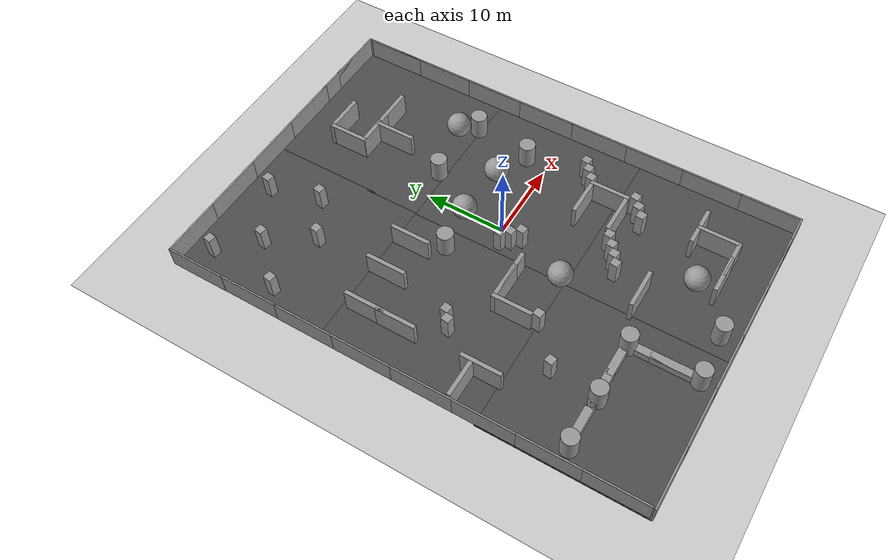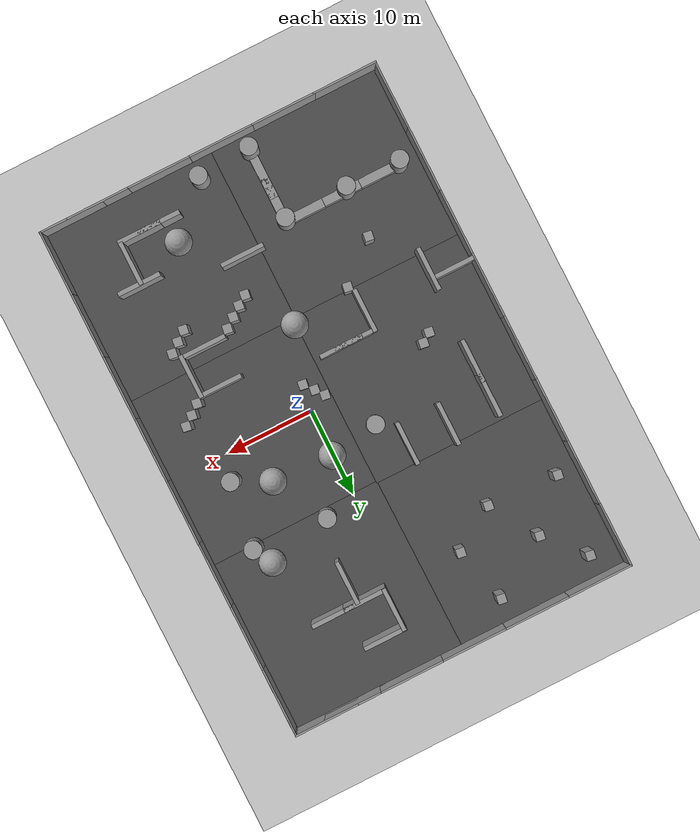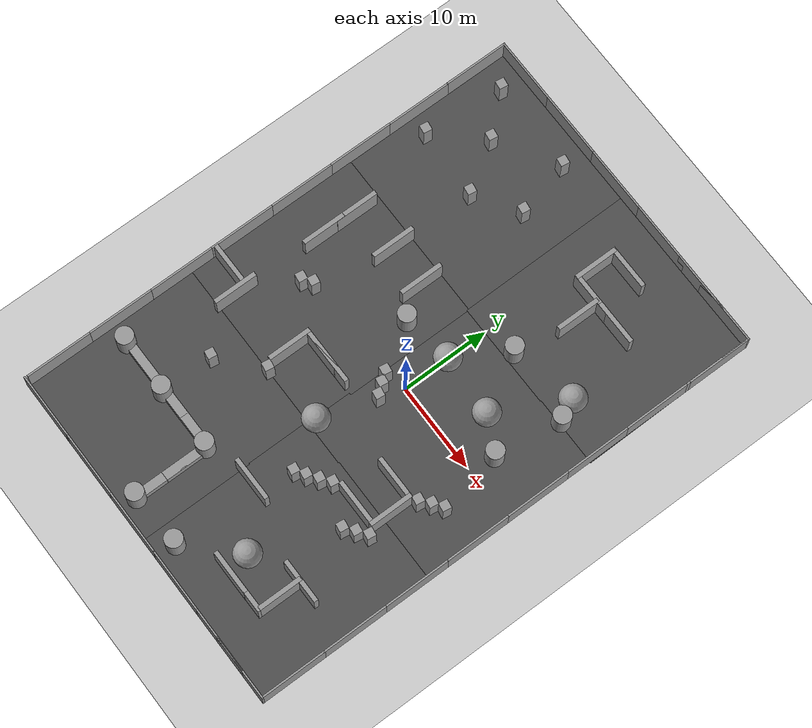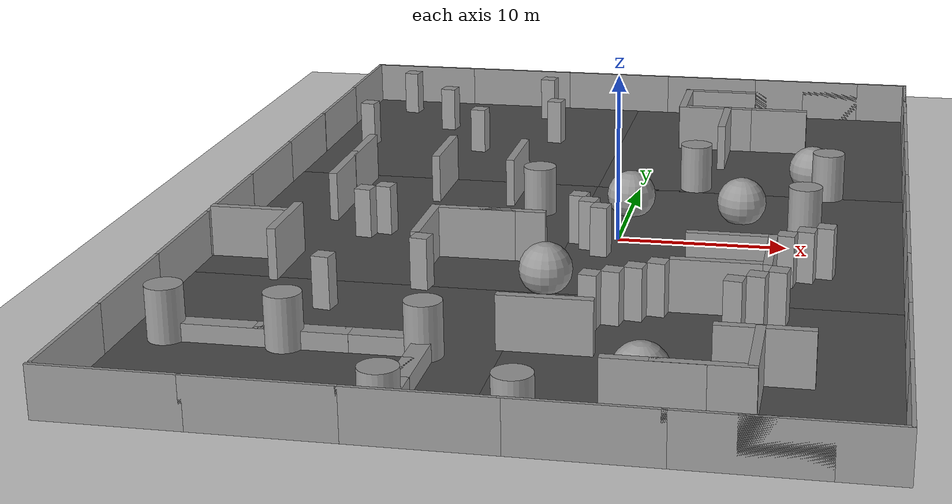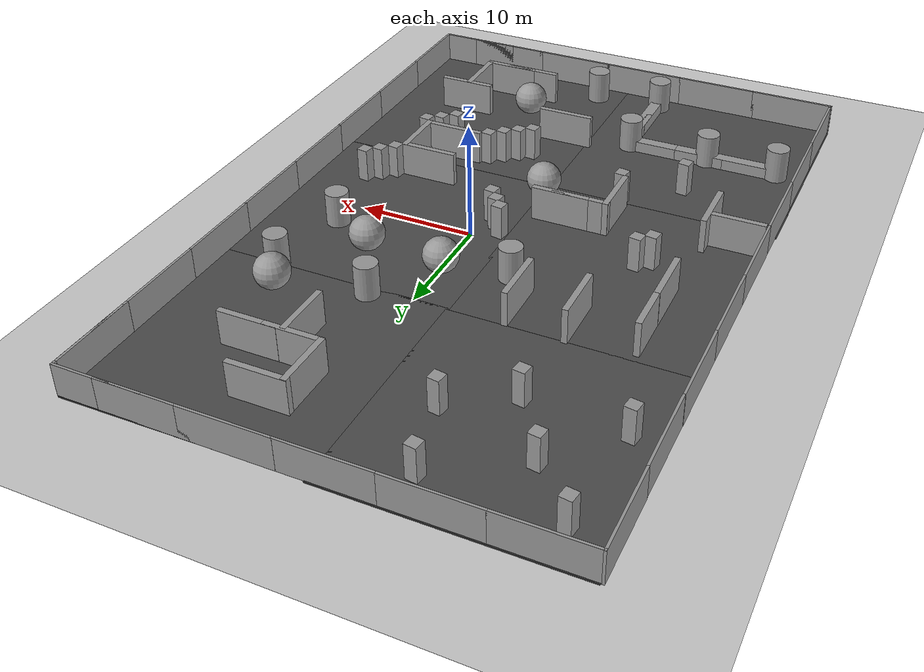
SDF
<sdf version="1.6">
 <world name="default">
  <light name="sun" type="directional">
   <pose>0 0 10 0 -0 0</pose>
   <diffuse>0.8 0.8 0.8 1</diffuse>
   <specular>0.2 0.2 0.2 1</specular>
   <attenuation>
    <range>1000</range>
    <constant>0.9</constant>
    <linear>0.01</linear>
    <quadratic>0.001</quadratic>
   </attenuation>
   <direction>-0.5 0.1 -0.9</direction>
  </light>
  <model name="ground_plane">
   <static>1</static>
   <link name="link">
    <collision name="collision">
     <geometry><plane><normal>0 0 1</normal><size>100 100</size></plane></geometry>
     <surface>
      <contact><collide_bitmask>65535</collide_bitmask></contact>
      <friction><ode><mu>100</mu><mu2>50</mu2></ode></friction>
     </surface>
    </collision>
    <visual name="visual">
     <cast_shadows>0</cast_shadows>
     <geometry><plane><normal>0 0 1</normal><size>100 100</size></plane></geometry>
     <material>
      <script><uri>file://media/materials/scripts/gazebo.material</uri><name>Gazebo/Grey</name></script>
     </material>
    </visual>
   </link>
  </model>
  <gravity>0 0 -9.8</gravity>
  <magnetic_field>6e-06 2.3e-05 -4.2e-05</magnetic_field>
  <atmosphere type="adiabatic"/>
  <physics name="default_physics" default="0" type="ode">
   <max_step_size>0.001</max_step_size>
   <real_time_factor>1</real_time_factor>
   <real_time_update_rate>1000</real_time_update_rate>
  </physics>
  <scene>
   <ambient>0.4 0.4 0.4 1</ambient>
   <background>0.7 0.7 0.7 1</background>
   <shadows>1</shadows>
   <sky><clouds><speed>12</speed></clouds></sky>
  </scene>
  <audio><device>default</device></audio>
  <spherical_coordinates>
   <surface_model>EARTH_WGS84</surface_model>
   <latitude_deg>0</latitude_deg>
   <longitude_deg>0</longitude_deg>
   <elevation>0</elevation>
   <heading_deg>0</heading_deg>
  </spherical_coordinates>
  <model name="asphalt_plane_0">
   <static>1</static>
   <link name="link">
    <collision name="collision"><geometry><box><size>20 20 0.1</size></box></geometry></collision>
    <visual name="visual">
     <cast_shadows>0</cast_shadows>
     <geometry><box><size>20 20 0.1</size></box></geometry>
     <material>
      <script>
       <uri>model://asphalt_plane/materials/scripts</uri>
       <uri>model://asphalt_plane/materials/textures</uri>
       <name>vrc/asphalt</name>
      </script>
     </material>
    </visual>
   </link>
   <pose>-12.8115 0.130544 0 0 -0 0</pose>
  </model>
  <model name="asphalt_plane_0_clone">
   <static>1</static>
   <link name="link">
    <collision name="collision"><geometry><box><size>20 20 0.1</size></box></geometry></collision>
    <visual name="visual">
     <cast_shadows>0</cast_shadows>
     <geometry><box><size>20 20 0.1</size></box></geometry>
     <material>
      <script>
       <uri>model://asphalt_plane/materials/scripts</uri>
       <uri>model://asphalt_plane/materials/textures</uri>
       <name>vrc/asphalt</name>
      </script>
     </material>
    </visual>
   </link>
   <pose>-13.0909 -19.8496 0 0 -0 0</pose>
  </model>
  <model name="asphalt_plane_0_clone_0">
   <static>1</static>
   <link name="link">
    <collision name="collision"><geometry><box><size>20 20 0.1</size></box></geometry></collision>
    <visual name="visual">
     <cast_shadows>0</cast_shadows>
     <geometry><box><size>20 20 0.1</size></box></geometry>
     <material>
      <script>
       <uri>model://asphalt_plane/materials/scripts</uri>
       <uri>model://asphalt_plane/materials/textures</uri>
       <name>vrc/asphalt</name>
      </script>
     </material>
    </visual>
   </link>
   <pose>6.79446 -19.8065 0 0 -0 0</pose>
  </model>
  <model name="asphalt_plane_0_clone_3">
   <static>1</static>
   <link name="link">
    <collision name="collision"><geometry><box><size>20 20 0.1</size></box></geometry></collision>
    <visual name="visual">
     <cast_shadows>0</cast_shadows>
     <geometry><box><size>20 20 0.1</size></box></geometry>
     <material>
      <script>
       <uri>model://asphalt_plane/materials/scripts</uri>
       <uri>model://asphalt_plane/materials/textures</uri>
       <name>vrc/asphalt</name>
      </script>
     </material>
    </visual>
   </link>
   <pose>7.00215 19.9777 0 0 -0 0.006913</pose>
  </model>
  <model name="asphalt_plane_0_clone_4">
   <static>1</static>
   <link name="asphalt_plane_0_clone_4::link">
    <collision name="collision"><geometry><box><size>20 20 0.1</size></box></geometry></collision>
    <visual name="visual">
     <cast_shadows>0</cast_shadows>
     <geometry><box><size>20 20 0.1</size></box></geometry>
     <material>
      <script>
       <uri>model://asphalt_plane/materials/scripts</uri>
       <uri>model://asphalt_plane/materials/textures</uri>
       <name>vrc/asphalt</name>
      </script>
     </material>
    </visual>
   </link>
   <pose>-12.7678 20.0846 0 0 -0 0</pose>
  </model>
  <model name="asphalt_plane_0_clone_0_clone">
   <static>1</static>
   <link name="link">
    <collision name="collision"><geometry><box><size>20 20 0.1</size></box></geometry></collision>
    <visual name="visual">
     <cast_shadows>0</cast_shadows>
     <geometry><box><size>20 20 0.1</size></box></geometry>
     <material>
      <script>
       <uri>model://asphalt_plane/materials/scripts</uri>
       <uri>model://asphalt_plane/materials/textures</uri>
       <name>vrc/asphalt</name>
      </script>
     </material>
    </visual>
   </link>
   <pose>6.94503 0.094695 0 0 -0 0</pose>
  </model>
  <model name="grey_wall">
   <static>1</static>
   <link name="link">
    <pose>0 0 1.4 0 -0 0</pose>
    <collision name="collision"><geometry><box><size>7.5 0.2 2.8</size></box></geometry></collision>
    <visual name="visual">
     <cast_shadows>0</cast_shadows>
     <geometry><box><size>7.5 0.2 2.8</size></box></geometry>
     <material>
      <script>
       <uri>model://grey_wall/materials/scripts</uri>
       <uri>model://grey_wall/materials/textures</uri>
       <name>vrc/grey_wall</name>
      </script>
     </material>
    </visual>
    <enable_wind>1</enable_wind>
   </link>
   <pose>-19.2347 29.9 0 0 -0 0</pose>
   <enable_wind>1</enable_wind>
  </model>
  <model name="grey_wall_clone">
   <static>1</static>
   <link name="link">
    <pose>0 0 1.4 0 -0 0</pose>
    <collision name="collision"><geometry><box><size>7.5 0.2 2.8</size></box></geometry></collision>
    <visual name="visual">
     <cast_shadows>0</cast_shadows>
     <geometry><box><size>7.5 0.2 2.8</size></box></geometry>
     <material>
      <script>
       <uri>model://grey_wall/materials/scripts</uri>
       <uri>model://grey_wall/materials/textures</uri>
       <name>vrc/grey_wall</name>
      </script>
     </material>
    </visual>
    <enable_wind>1</enable_wind>
   </link>
   <pose>-11.7883 29.9 0 0 -0 0</pose>
   <enable_wind>1</enable_wind>
  </model>
  <model name="grey_wall_clone_clone">
   <static>1</static>
   <link name="link">
    <pose>0 0 1.4 0 -0 0</pose>
    <collision name="collision"><geometry><box><size>7.5 0.2 2.8</size></box></geometry></collision>
    <visual name="visual">
     <cast_shadows>0</cast_shadows>
     <geometry><box><size>7.5 0.2 2.8</size></box></geometry>
     <material>
      <script>
       <uri>model://grey_wall/materials/scripts</uri>
       <uri>model://grey_wall/materials/textures</uri>
       <name>vrc/grey_wall</name>
      </script>
     </material>
    </visual>
    <enable_wind>1</enable_wind>
   </link>
   <pose>-4.30755 29.8961 0 0 -0 0</pose>
   <enable_wind>1</enable_wind>
  </model>
  <model name="grey_wall_clone_clone_0">
   <static>1</static>
   <link name="link">
    <pose>0 0 1.4 0 -0 0</pose>
    <collision name="collision"><geometry><box><size>7.5 0.2 2.8</size></box></geometry></collision>
    <visual name="visual">
     <cast_shadows>0</cast_shadows>
     <geometry><box><size>7.5 0.2 2.8</size></box></geometry>
     <material>
      <script>
       <uri>model://grey_wall/materials/scripts</uri>
       <uri>model://grey_wall/materials/textures</uri>
       <name>vrc/grey_wall</name>
      </script>
     </material>
    </visual>
    <enable_wind>1</enable_wind>
   </link>
   <pose>3.08937 29.9 0 0 -0 0</pose>
   <enable_wind>1</enable_wind>
  </model>
  <model name="grey_wall_clone_clone_1">
   <static>1</static>
   <link name="link">
    <pose>0 0 1.4 0 -0 0</pose>
    <collision name="collision"><geometry><box><size>7.5 0.2 2.8</size></box></geometry></collision>
    <visual name="visual">
     <cast_shadows>0</cast_shadows>
     <geometry><box><size>7.5 0.2 2.8</size></box></geometry>
     <material>
      <script>
       <uri>model://grey_wall/materials/scripts</uri>
       <uri>model://grey_wall/materials/textures</uri>
       <name>vrc/grey_wall</name>
      </script>
     </material>
    </visual>
    <enable_wind>1</enable_wind>
   </link>
   <pose>13.265 29.9 0 0 -0 0</pose>
   <enable_wind>1</enable_wind>
  </model>
  <model name="grey_wall_clone_clone_2">
   <static>1</static>
   <link name="link">
    <pose>0 0 1.4 0 -0 0</pose>
    <collision name="collision"><geometry><box><size>7.5 0.2 2.8</size></box></geometry></collision>
    <visual name="visual">
     <cast_shadows>0</cast_shadows>
     <geometry><box><size>7.5 0.2 2.8</size></box></geometry>
     <material>
      <script>
       <uri>model://grey_wall/materials/scripts</uri>
       <uri>model://grey_wall/materials/textures</uri>
       <name>vrc/grey_wall</name>
      </script>
     </material>
    </visual>
    <enable_wind>1</enable_wind>
   </link>
   <pose>9.74436 29.9 0 0 -0 0</pose>
   <enable_wind>1</enable_wind>
  </model>
  <model name="grey_wall_clone_clone_3">
   <static>1</static>
   <link name="link">
    <pose>0 0 1.4 0 -0 0</pose>
    <collision name="collision"><geometry><box><size>7.5 0.2 2.8</size></box></geometry></collision>
    <visual name="visual">
     <cast_shadows>0</cast_shadows>
     <geometry><box><size>7.5 0.2 2.8</size></box></geometry>
     <material>
      <script>
       <uri>model://grey_wall/materials/scripts</uri>
       <uri>model://grey_wall/materials/textures</uri>
       <name>vrc/grey_wall</name>
      </script>
     </material>
    </visual>
    <enable_wind>1</enable_wind>
   </link>
   <pose>16.9 -26.2145 0 0 -0 1.5707</pose>
   <enable_wind>1</enable_wind>
  </model>
  <model name="grey_wall_clone_clone_3_clone">
   <static>1</static>
   <link name="link">
    <pose>0 0 1.4 0 -0 0</pose>
    <collision name="collision"><geometry><box><size>7.5 0.2 2.8</size></box></geometry></collision>
    <visual name="visual">
     <cast_shadows>0</cast_shadows>
     <geometry><box><size>7.5 0.2 2.8</size></box></geometry>
     <material>
      <script>
       <uri>model://grey_wall/materials/scripts</uri>
       <uri>model://grey_wall/materials/textures</uri>
       <name>vrc/grey_wall</name>
      </script>
     </material>
    </visual>
    <enable_wind>1</enable_wind>
   </link>
   <pose>16.9 -18.8421 0 0 -0 1.5707</pose>
   <enable_wind>1</enable_wind>
  </model>
  <model name="grey_wall_clone_clone_3_clone_0">
   <static>1</static>
   <link name="link">
    <pose>0 0 1.4 0 -0 0</pose>
    <collision name="collision"><geometry><box><size>7.5 0.2 2.8</size></box></geometry></collision>
    <visual name="visual">
     <cast_shadows>0</cast_shadows>
     <geometry><box><size>7.5 0.2 2.8</size></box></geometry>
     <material>
      <script>
       <uri>model://grey_wall/materials/scripts</uri>
       <uri>model://grey_wall/materials/textures</uri>
       <name>vrc/grey_wall</name>
      </script>
     </material>
    </visual>
    <enable_wind>1</enable_wind>
   </link>
   <pose>16.9 -11.3736 0 0 -0 1.5707</pose>
   <enable_wind>1</enable_wind>
  </model>
  <model name="grey_wall_clone_clone_3_clone_1">
   <static>1</static>
   <link name="link">
    <pose>0 0 1.4 0 -0 0</pose>
    <collision name="collision"><geometry><box><size>7.5 0.2 2.8</size></box></geometry></collision>
    <visual name="visual">
     <cast_shadows>0</cast_shadows>
     <geometry><box><size>7.5 0.2 2.8</size></box></geometry>
     <material>
      <script>
       <uri>model://grey_wall/materials/scripts</uri>
       <uri>model://grey_wall/materials/textures</uri>
       <name>vrc/grey_wall</name>
      </script>
     </material>
    </visual>
    <enable_wind>1</enable_wind>
   </link>
   <pose>16.9 -3.99436 0 0 -0 1.5707</pose>
   <enable_wind>1</enable_wind>
  </model>
  <model name="grey_wall_clone_clone_3_clone_2">
   <static>1</static>
   <link name="link">
    <pose>0 0 1.4 0 -0 0</pose>
    <collision name="collision"><geometry><box><size>7.5 0.2 2.8</size></box></geometry></collision>
    <visual name="visual">
     <cast_shadows>0</cast_shadows>
     <geometry><box><size>7.5 0.2 2.8</size></box></geometry>
     <material>
      <script>
       <uri>model://grey_wall/materials/scripts</uri>
       <uri>model://grey_wall/materials/textures</uri>
       <name>vrc/grey_wall</name>
      </script>
     </material>
    </visual>
    <enable_wind>1</enable_wind>
   </link>
   <pose>16.9 3.42698 0 0 -0 1.5707</pose>
   <enable_wind>1</enable_wind>
  </model>
  <model name="grey_wall_clone_clone_3_clone_3">
   <static>1</static>
   <link name="link">
    <pose>0 0 1.4 0 -0 0</pose>
    <collision name="collision"><geometry><box><size>7.5 0.2 2.8</size></box></geometry></collision>
    <visual name="visual">
     <cast_shadows>0</cast_shadows>
     <geometry><box><size>7.5 0.2 2.8</size></box></geometry>
     <material>
      <script>
       <uri>model://grey_wall/materials/scripts</uri>
       <uri>model://grey_wall/materials/textures</uri>
       <name>vrc/grey_wall</name>
      </script>
     </material>
    </visual>
    <enable_wind>1</enable_wind>
   </link>
   <pose>16.9 10.8599 0 0 -0 1.5707</pose>
   <enable_wind>1</enable_wind>
  </model>
  <model name="grey_wall_clone_clone_3_clone_4">
   <static>1</static>
   <link name="link">
    <pose>0 0 1.4 0 -0 0</pose>
    <collision name="collision"><geometry><box><size>7.5 0.2 2.8</size></box></geometry></collision>
    <visual name="visual">
     <cast_shadows>0</cast_shadows>
     <geometry><box><size>7.5 0.2 2.8</size></box></geometry>
     <material>
      <script>
       <uri>model://grey_wall/materials/scripts</uri>
       <uri>model://grey_wall/materials/textures</uri>
       <name>vrc/grey_wall</name>
      </script>
     </material>
    </visual>
    <enable_wind>1</enable_wind>
   </link>
   <pose>16.9 18.3261 0 0 -0 1.5707</pose>
   <enable_wind>1</enable_wind>
  </model>
  <model name="grey_wall_clone_clone_3_clone_5">
   <static>1</static>
   <link name="link">
    <pose>0 0 1.4 0 -0 0</pose>
    <collision name="collision"><geometry><box><size>7.5 0.2 2.8</size></box></geometry></collision>
    <visual name="visual">
     <cast_shadows>0</cast_shadows>
     <geometry><box><size>7.5 0.2 2.8</size></box></geometry>
     <material>
      <script>
       <uri>model://grey_wall/materials/scripts</uri>
       <uri>model://grey_wall/materials/textures</uri>
       <name>vrc/grey_wall</name>
      </script>
     </material>
    </visual>
    <enable_wind>1</enable_wind>
   </link>
   <pose>16.9 25.8035 0 0 -0 1.5707</pose>
   <enable_wind>1</enable_wind>
  </model>
  <model name="grey_wall_clone_clone_3_clone_6">
   <static>1</static>
   <link name="link">
    <pose>0 0 1.4 0 -0 0</pose>
    <collision name="collision"><geometry><box><size>7.5 0.2 2.8</size></box></geometry></collision>
    <visual name="visual">
     <cast_shadows>0</cast_shadows>
     <geometry><box><size>7.5 0.2 2.8</size></box></geometry>
     <material>
      <script>
       <uri>model://grey_wall/materials/scripts</uri>
       <uri>model://grey_wall/materials/textures</uri>
       <name>vrc/grey_wall</name>
      </script>
     </material>
    </visual>
    <enable_wind>1</enable_wind>
   </link>
   <pose>-22.9 26.2649 0 0 -0 1.5707</pose>
   <enable_wind>1</enable_wind>
  </model>
  <model name="grey_wall_clone_clone_3_clone_6_clone">
   <static>1</static>
   <link name="link">
    <pose>0 0 1.4 0 -0 0</pose>
    <collision name="collision"><geometry><box><size>7.5 0.2 2.8</size></box></geometry></collision>
    <visual name="visual">
     <cast_shadows>0</cast_shadows>
     <geometry><box><size>7.5 0.2 2.8</size></box></geometry>
     <material>
      <script>
       <uri>model://grey_wall/materials/scripts</uri>
       <uri>model://grey_wall/materials/textures</uri>
       <name>vrc/grey_wall</name>
      </script>
     </material>
    </visual>
    <enable_wind>1</enable_wind>
   </link>
   <pose>-22.8768 18.8737 0 0 -0 1.5707</pose>
   <enable_wind>1</enable_wind>
  </model>
  <model name="grey_wall_clone_clone_3_clone_6_clone_0">
   <static>1</static>
   <link name="link">
    <pose>0 0 1.4 0 -0 0</pose>
    <collision name="collision"><geometry><box><size>7.5 0.2 2.8</size></box></geometry></collision>
    <visual name="visual">
     <cast_shadows>0</cast_shadows>
     <geometry><box><size>7.5 0.2 2.8</size></box></geometry>
     <material>
      <script>
       <uri>model://grey_wall/materials/scripts</uri>
       <uri>model://grey_wall/materials/textures</uri>
       <name>vrc/grey_wall</name>
      </script>
     </material>
    </visual>
    <enable_wind>1</enable_wind>
   </link>
   <pose>-22.9 11.4792 0 0 -0 1.5707</pose>
   <enable_wind>1</enable_wind>
  </model>
  <model name="grey_wall_clone_clone_3_clone_6_clone_1">
   <static>1</static>
   <link name="link">
    <pose>0 0 1.4 0 -0 0</pose>
    <collision name="collision"><geometry><box><size>7.5 0.2 2.8</size></box></geometry></collision>
    <visual name="visual">
     <cast_shadows>0</cast_shadows>
     <geometry><box><size>7.5 0.2 2.8</size></box></geometry>
     <material>
      <script>
       <uri>model://grey_wall/materials/scripts</uri>
       <uri>model://grey_wall/materials/textures</uri>
       <name>vrc/grey_wall</name>
      </script>
     </material>
    </visual>
    <enable_wind>1</enable_wind>
   </link>
   <pose>-22.9 4.04638 0 0 -0 1.5707</pose>
   <enable_wind>1</enable_wind>
  </model>
  <model name="grey_wall_clone_clone_3_clone_6_clone_2">
   <static>1</static>
   <link name="link">
    <pose>0 0 1.4 0 -0 0</pose>
    <collision name="collision"><geometry><box><size>7.5 0.2 2.8</size></box></geometry></collision>
    <visual name="visual">
     <cast_shadows>0</cast_shadows>
     <geometry><box><size>7.5 0.2 2.8</size></box></geometry>
     <material>
      <script>
       <uri>model://grey_wall/materials/scripts</uri>
       <uri>model://grey_wall/materials/textures</uri>
       <name>vrc/grey_wall</name>
      </script>
     </material>
    </visual>
    <enable_wind>1</enable_wind>
   </link>
   <pose>-22.9 -3.44017 0 0 -0 1.5707</pose>
   <enable_wind>1</enable_wind>
  </model>
  <model name="grey_wall_clone_clone_3_clone_6_clone_3">
   <static>1</static>
   <link name="link">
    <pose>0 0 1.4 0 -0 0</pose>
    <collision name="collision"><geometry><box><size>7.5 0.2 2.8</size></box></geometry></collision>
    <visual name="visual">
     <cast_shadows>0</cast_shadows>
     <geometry><box><size>7.5 0.2 2.8</size></box></geometry>
     <material>
      <script>
       <uri>model://grey_wall/materials/scripts</uri>
       <uri>model://grey_wall/materials/textures</uri>
       <name>vrc/grey_wall</name>
      </script>
     </material>
    </visual>
    <enable_wind>1</enable_wind>
   </link>
   <pose>-22.9 -10.9196 0 0 -0 1.5707</pose>
   <enable_wind>1</enable_wind>
  </model>
  <model name="grey_wall_clone_clone_3_clone_6_clone_4">
   <static>1</static>
   <link name="link">
    <pose>0 0 1.4 0 -0 0</pose>
    <collision name="collision"><geometry><box><size>7.5 0.2 2.8</size></box></geometry></collision>
    <visual name="visual">
     <cast_shadows>0</cast_shadows>
     <geometry><box><size>7.5 0.2 2.8</size></box></geometry>
     <material>
      <script>
       <uri>model://grey_wall/materials/scripts</uri>
       <uri>model://grey_wall/materials/textures</uri>
       <name>vrc/grey_wall</name>
      </script>
     </material>
    </visual>
    <enable_wind>1</enable_wind>
   </link>
   <pose>-22.9 -18.392 0 0 -0 1.5707</pose>
   <enable_wind>1</enable_wind>
  </model>
  <model name="grey_wall_clone_clone_3_clone_6_clone_5">
   <static>1</static>
   <link name="link">
    <pose>0 0 1.4 0 -0 0</pose>
    <collision name="collision"><geometry><box><size>7.5 0.2 2.8</size></box></geometry></collision>
    <visual name="visual">
     <cast_shadows>0</cast_shadows>
     <geometry><box><size>7.5 0.2 2.8</size></box></geometry>
     <material>
      <script>
       <uri>model://grey_wall/materials/scripts</uri>
       <uri>model://grey_wall/materials/textures</uri>
       <name>vrc/grey_wall</name>
      </script>
     </material>
    </visual>
    <enable_wind>1</enable_wind>
   </link>
   <pose>-22.9 -25.8809 0 0 -0 1.5707</pose>
   <enable_wind>1</enable_wind>
  </model>
  <model name="grey_wall_clone_0">
   <static>1</static>
   <link name="link">
    <pose>0 0 1.4 0 -0 0</pose>
    <collision name="collision"><geometry><box><size>7.5 0.2 2.8</size></box></geometry></collision>
    <visual name="visual">
     <cast_shadows>0</cast_shadows>
     <geometry><box><size>7.5 0.2 2.8</size></box></geometry>
     <material>
      <script>
       <uri>model://grey_wall/materials/scripts</uri>
       <uri>model://grey_wall/materials/textures</uri>
       <name>vrc/grey_wall</name>
      </script>
     </material>
    </visual>
    <enable_wind>1</enable_wind>
   </link>
   <pose>-19.3 -29.9 0 0 -0 0</pose>
   <enable_wind>1</enable_wind>
  </model>
  <model name="grey_wall_clone_1">
   <static>1</static>
   <link name="link">
    <pose>0 0 1.4 0 -0 0</pose>
    <collision name="collision"><geometry><box><size>7.5 0.2 2.8</size></box></geometry></collision>
    <visual name="visual">
     <cast_shadows>0</cast_shadows>
     <geometry><box><size>7.5 0.2 2.8</size></box></geometry>
     <material>
      <script>
       <uri>model://grey_wall/materials/scripts</uri>
       <uri>model://grey_wall/materials/textures</uri>
       <name>vrc/grey_wall</name>
      </script>
     </material>
    </visual>
    <enable_wind>1</enable_wind>
   </link>
   <pose>-11.9819 -29.9 0 0 -0 0</pose>
   <enable_wind>1</enable_wind>
  </model>
  <model name="grey_wall_clone_2">
   <static>1</static>
   <link name="link">
    <pose>0 0 1.4 0 -0 0</pose>
    <collision name="collision"><geometry><box><size>7.5 0.2 2.8</size></box></geometry></collision>
    <visual name="visual">
     <cast_shadows>0</cast_shadows>
     <geometry><box><size>7.5 0.2 2.8</size></box></geometry>
     <material>
      <script>
       <uri>model://grey_wall/materials/scripts</uri>
       <uri>model://grey_wall/materials/textures</uri>
       <name>vrc/grey_wall</name>
      </script>
     </material>
    </visual>
    <enable_wind>1</enable_wind>
   </link>
   <pose>-4.58635 -29.9 0 0 -0 0</pose>
   <enable_wind>1</enable_wind>
  </model>
  <model name="grey_wall_clone_3">
   <static>1</static>
   <link name="link">
    <pose>0 0 1.4 0 -0 0</pose>
    <collision name="collision"><geometry><box><size>7.5 0.2 2.8</size></box></geometry></collision>
    <visual name="visual">
     <cast_shadows>0</cast_shadows>
     <geometry><box><size>7.5 0.2 2.8</size></box></geometry>
     <material>
      <script>
       <uri>model://grey_wall/materials/scripts</uri>
       <uri>model://grey_wall/materials/textures</uri>
       <name>vrc/grey_wall</name>
      </script>
     </material>
    </visual>
    <enable_wind>1</enable_wind>
   </link>
   <pose>2.73201 -29.9 0 0 -0 0</pose>
   <enable_wind>1</enable_wind>
  </model>
  <model name="grey_wall_clone_4">
   <static>1</static>
   <link name="link">
    <pose>0 0 1.4 0 -0 0</pose>
    <collision name="collision"><geometry><box><size>7.5 0.2 2.8</size></box></geometry></collision>
    <visual name="visual">
     <cast_shadows>0</cast_shadows>
     <geometry><box><size>7.5 0.2 2.8</size></box></geometry>
     <material>
      <script>
       <uri>model://grey_wall/materials/scripts</uri>
       <uri>model://grey_wall/materials/textures</uri>
       <name>vrc/grey_wall</name>
      </script>
     </material>
    </visual>
    <enable_wind>1</enable_wind>
   </link>
   <pose>9.96239 -29.9 0 0 -0 0</pose>
   <enable_wind>1</enable_wind>
  </model>
  <model name="grey_wall_clone_5">
   <static>1</static>
   <link name="link">
    <pose>0 0 1.4 0 -0 0</pose>
    <collision name="collision"><geometry><box><size>7.5 0.2 2.8</size></box></geometry></collision>
    <visual name="visual">
     <cast_shadows>0</cast_shadows>
     <geometry><box><size>7.5 0.2 2.8</size></box></geometry>
     <material>
      <script>
       <uri>model://grey_wall/materials/scripts</uri>
       <uri>model://grey_wall/materials/textures</uri>
       <name>vrc/grey_wall</name>
      </script>
     </material>
    </visual>
    <enable_wind>1</enable_wind>
   </link>
   <pose>13.258 -29.9 0 0 -0 0</pose>
   <enable_wind>1</enable_wind>
  </model>
  <model name="grey_wall_clone_clone_3_clone_5_clone">
   <static>1</static>
   <link name="link">
    <pose>0 0 1.4 0 -0 0</pose>
    <collision name="collision"><geometry><box><size>7.5 0.2 2.8</size></box></geometry></collision>
    <visual name="visual">
     <cast_shadows>0</cast_shadows>
     <geometry><box><size>7.5 0.2 2.8</size></box></geometry>
     <material>
      <script>
       <uri>model://grey_wall/materials/scripts</uri>
       <uri>model://grey_wall/materials/textures</uri>
       <name>vrc/grey_wall</name>
      </script>
     </material>
    </visual>
    <enable_wind>1</enable_wind>
   </link>
   <pose>16.907 26.2365 0 0 -0 1.5707</pose>
   <enable_wind>1</enable_wind>
  </model>
  <model name="unit_box_x_horiz">
   <link name="link">
    <inertial>
     <mass>1</mass>
     <inertia>
      <ixx>0.166667</ixx>
      <ixy>0</ixy>
      <ixz>0</ixz>
      <iyy>0.166667</iyy>
      <iyz>0</iyz>
      <izz>0.166667</izz>
     </inertia>
    </inertial>
    <visual name="visual">
     <geometry><box><size>5 0.5 3</size></box></geometry>
     <material>
      <script><name>Gazebo/Grey</name><uri>file://media/materials/scripts/gazebo.material</uri></script>
      <shader type="pixel"><normal_map>__default__</normal_map></shader>
      <ambient>0.3 0.3 0.3 1</ambient>
      <diffuse>0.7 0.7 0.7 1</diffuse>
      <specular>0.01 0.01 0.01 1</specular>
      <emissive>0 0 0 1</emissive>
     </material>
    </visual>
    <collision name="collision">
     <geometry><box><size>5 1 3</size></box></geometry>
     <surface>
      <friction>
       <ode><mu>1</mu><mu2>1</mu2><fdir1>0 0 0</fdir1><slip1>0</slip1><slip2>0</slip2></ode>
       <torsional>
        <coefficient>1</coefficient>
        <patch_radius>0</patch_radius>
        <surface_radius>0</surface_radius>
        <use_patch_radius>1</use_patch_radius>
        <ode><slip>0</slip></ode>
       </torsional>
      </friction>
      <bounce><restitution_coefficient>0</restitution_coefficient><threshold>1e+06</threshold></bounce>
      <contact>
       <collide_without_contact>0</collide_without_contact>
       <collide_without_contact_bitmask>1</collide_without_contact_bitmask>
       <collide_bitmask>1</collide_bitmask>
       <ode>
        <soft_cfm>0</soft_cfm>
        <soft_erp>0.2</soft_erp>
        <kp>1e+13</kp>
        <kd>1</kd>
        <max_vel>0.01</max_vel>
        <min_depth>0</min_depth>
       </ode>
       <bullet>
        <split_impulse>1</split_impulse>
        <split_impulse_penetration_threshold>-0.01</split_impulse_penetration_threshold>
        <soft_cfm>0</soft_cfm>
        <soft_erp>0.2</soft_erp>
        <kp>1e+13</kp>
        <kd>1</kd>
       </bullet>
      </contact>
     </surface>
    </collision>
   </link>
   <static>1</static>
   <pose>3.83307 24.9531 1.54702 0 -0 6.7e-05</pose>
  </model>
  <model name="unit_box_x_horiz_clone">
   <link name="link">
    <inertial>
     <mass>1</mass>
     <inertia>
      <ixx>0.166667</ixx>
      <ixy>0</ixy>
      <ixz>0</ixz>
      <iyy>0.166667</iyy>
      <iyz>0</iyz>
      <izz>0.166667</izz>
     </inertia>
    </inertial>
    <visual name="visual">
     <geometry><box><size>5 0.5 3</size></box></geometry>
     <material>
      <script><name>Gazebo/Grey</name><uri>file://media/materials/scripts/gazebo.material</uri></script>
      <shader type="pixel"><normal_map>__default__</normal_map></shader>
      <ambient>0.3 0.3 0.3 1</ambient>
      <diffuse>0.7 0.7 0.7 1</diffuse>
      <specular>0.01 0.01 0.01 1</specular>
      <emissive>0 0 0 1</emissive>
     </material>
    </visual>
    <collision name="collision">
     <geometry><box><size>5 1 3</size></box></geometry>
     <surface>
      <friction>
       <ode><mu>1</mu><mu2>1</mu2><fdir1>0 0 0</fdir1><slip1>0</slip1><slip2>0</slip2></ode>
       <torsional>
        <coefficient>1</coefficient>
        <patch_radius>0</patch_radius>
        <surface_radius>0</surface_radius>
        <use_patch_radius>1</use_patch_radius>
        <ode><slip>0</slip></ode>
       </torsional>
      </friction>
      <bounce><restitution_coefficient>0</restitution_coefficient><threshold>1e+06</threshold></bounce>
      <contact>
       <collide_without_contact>0</collide_without_contact>
       <collide_without_contact_bitmask>1</collide_without_contact_bitmask>
       <collide_bitmask>1</collide_bitmask>
       <ode>
        <soft_cfm>0</soft_cfm>
        <soft_erp>0.2</soft_erp>
        <kp>1e+13</kp>
        <kd>1</kd>
        <max_vel>0.01</max_vel>
        <min_depth>0</min_depth>
       </ode>
       <bullet>
        <split_impulse>1</split_impulse>
        <split_impulse_penetration_threshold>-0.01</split_impulse_penetration_threshold>
        <soft_cfm>0</soft_cfm>
        <soft_erp>0.2</soft_erp>
        <kp>1e+13</kp>
        <kd>1</kd>
       </bullet>
      </contact>
     </surface>
    </collision>
   </link>
   <static>1</static>
   <pose>3.88957 20.3551 1.54702 0 -0 6.7e-05</pose>
  </model>
  <model name="unit_box_x_horiz_clone_0">
   <link name="link">
    <inertial>
     <mass>1</mass>
     <inertia>
      <ixx>0.166667</ixx>
      <ixy>0</ixy>
      <ixz>0</ixz>
      <iyy>0.166667</iyy>
      <iyz>0</iyz>
      <izz>0.166667</izz>
     </inertia>
    </inertial>
    <visual name="visual">
     <geometry><box><size>5 0.5 3</size></box></geometry>
     <material>
      <script><name>Gazebo/Grey</name><uri>file://media/materials/scripts/gazebo.material</uri></script>
      <shader type="pixel"><normal_map>__default__</normal_map></shader>
      <ambient>0.3 0.3 0.3 1</ambient>
      <diffuse>0.7 0.7 0.7 1</diffuse>
      <specular>0.01 0.01 0.01 1</specular>
      <emissive>0 0 0 1</emissive>
     </material>
    </visual>
    <collision name="collision">
     <geometry><box><size>5 1 3</size></box></geometry>
     <surface>
      <friction>
       <ode><mu>1</mu><mu2>1</mu2><fdir1>0 0 0</fdir1><slip1>0</slip1><slip2>0</slip2></ode>
       <torsional>
        <coefficient>1</coefficient>
        <patch_radius>0</patch_radius>
        <surface_radius>0</surface_radius>
        <use_patch_radius>1</use_patch_radius>
        <ode><slip>0</slip></ode>
       </torsional>
      </friction>
      <bounce><restitution_coefficient>0</restitution_coefficient><threshold>1e+06</threshold></bounce>
      <contact>
       <collide_without_contact>0</collide_without_contact>
       <collide_without_contact_bitmask>1</collide_without_contact_bitmask>
       <collide_bitmask>1</collide_bitmask>
       <ode>
        <soft_cfm>0</soft_cfm>
        <soft_erp>0.2</soft_erp>
        <kp>1e+13</kp>
        <kd>1</kd>
        <max_vel>0.01</max_vel>
        <min_depth>0</min_depth>
       </ode>
       <bullet>
        <split_impulse>1</split_impulse>
        <split_impulse_penetration_threshold>-0.01</split_impulse_penetration_threshold>
        <soft_cfm>0</soft_cfm>
        <soft_erp>0.2</soft_erp>
        <kp>1e+13</kp>
        <kd>1</kd>
       </bullet>
      </contact>
     </surface>
    </collision>
   </link>
   <static>1</static>
   <pose>7.68173 20.3603 1.54702 0 -0 6.7e-05</pose>
  </model>
  <model name="unit_box_clone">
   <link name="link">
    <inertial>
     <mass>1</mass>
     <inertia>
      <ixx>0.166667</ixx>
      <ixy>0</ixy>
      <ixz>0</ixz>
      <iyy>0.166667</iyy>
      <iyz>0</iyz>
      <izz>0.166667</izz>
     </inertia>
    </inertial>
    <visual name="visual">
     <geometry><box><size>0.5 5 3</size></box></geometry>
     <material>
      <script><name>Gazebo/Grey</name><uri>file://media/materials/scripts/gazebo.material</uri></script>
      <shader type="pixel"><normal_map>__default__</normal_map></shader>
      <ambient>0.3 0.3 0.3 1</ambient>
      <diffuse>0.7 0.7 0.7 1</diffuse>
      <specular>0.01 0.01 0.01 1</specular>
      <emissive>0 0 0 1</emissive>
     </material>
    </visual>
    <collision name="collision">
     <geometry><box><size>1 5 3</size></box></geometry>
     <surface>
      <friction>
       <ode><mu>1</mu><mu2>1</mu2><fdir1>0 0 0</fdir1><slip1>0</slip1><slip2>0</slip2></ode>
       <torsional>
        <coefficient>1</coefficient>
        <patch_radius>0</patch_radius>
        <surface_radius>0</surface_radius>
        <use_patch_radius>1</use_patch_radius>
        <ode><slip>0</slip></ode>
       </torsional>
      </friction>
      <bounce><restitution_coefficient>0</restitution_coefficient><threshold>1e+06</threshold></bounce>
      <contact>
       <collide_without_contact>0</collide_without_contact>
       <collide_without_contact_bitmask>1</collide_without_contact_bitmask>
       <collide_bitmask>1</collide_bitmask>
       <ode>
        <soft_cfm>0</soft_cfm>
        <soft_erp>0.2</soft_erp>
        <kp>1e+13</kp>
        <kd>1</kd>
        <max_vel>0.01</max_vel>
        <min_depth>0</min_depth>
       </ode>
       <bullet>
        <split_impulse>1</split_impulse>
        <split_impulse_penetration_threshold>-0.01</split_impulse_penetration_threshold>
        <soft_cfm>0</soft_cfm>
        <soft_erp>0.2</soft_erp>
        <kp>1e+13</kp>
        <kd>1</kd>
       </bullet>
      </contact>
     </surface>
    </collision>
   </link>
   <static>1</static>
   <pose>1.60803 22.6446 1.54724 0 -0 6.7e-05</pose>
  </model>
  <model name="unit_box_1">
   <link name="link">
    <inertial>
     <mass>1</mass>
     <inertia>
      <ixx>0.166667</ixx>
      <ixy>0</ixy>
      <ixz>0</ixz>
      <iyy>0.166667</iyy>
      <iyz>0</iyz>
      <izz>0.166667</izz>
     </inertia>
    </inertial>
    <visual name="visual">
     <geometry><box><size>1 1 3</size></box></geometry>
     <material>
      <script><name>Gazebo/Grey</name><uri>file://media/materials/scripts/gazebo.material</uri></script>
      <shader type="pixel"><normal_map>__default__</normal_map></shader>
      <ambient>0.3 0.3 0.3 1</ambient>
      <diffuse>0.7 0.7 0.7 1</diffuse>
      <specular>0.01 0.01 0.01 1</specular>
      <emissive>0 0 0 1</emissive>
     </material>
    </visual>
    <collision name="collision">
     <geometry><box><size>1 1 3</size></box></geometry>
     <surface>
      <friction>
       <ode><mu>1</mu><mu2>1</mu2><fdir1>0 0 0</fdir1><slip1>0</slip1><slip2>0</slip2></ode>
       <torsional>
        <coefficient>1</coefficient>
        <patch_radius>0</patch_radius>
        <surface_radius>0</surface_radius>
        <use_patch_radius>1</use_patch_radius>
        <ode><slip>0</slip></ode>
       </torsional>
      </friction>
      <bounce><restitution_coefficient>0</restitution_coefficient><threshold>1e+06</threshold></bounce>
      <contact>
       <collide_without_contact>0</collide_without_contact>
       <collide_without_contact_bitmask>1</collide_without_contact_bitmask>
       <collide_bitmask>1</collide_bitmask>
       <ode>
        <soft_cfm>0</soft_cfm>
        <soft_erp>0.2</soft_erp>
        <kp>1e+13</kp>
        <kd>1</kd>
        <max_vel>0.01</max_vel>
        <min_depth>0</min_depth>
       </ode>
       <bullet>
        <split_impulse>1</split_impulse>
        <split_impulse_penetration_threshold>-0.01</split_impulse_penetration_threshold>
        <soft_cfm>0</soft_cfm>
        <soft_erp>0.2</soft_erp>
        <kp>1e+13</kp>
        <kd>1</kd>
       </bullet>
      </contact>
     </surface>
    </collision>
   </link>
   <static>1</static>
   <pose>-9.0508 26.7938 1.52567 0 0 -0.143769</pose>
  </model>
  <model name="unit_sphere_clone">
   <link name="link">
    <inertial>
     <mass>1</mass>
     <inertia><ixx>0.1</ixx><ixy>0</ixy><ixz>0</ixz><iyy>0.1</iyy><iyz>0</iyz><izz>0.1</izz></inertia>
    </inertial>
    <visual name="visual">
     <geometry><sphere><radius>1.5</radius></sphere></geometry>
     <material>
      <script><name>Gazebo/Grey</name><uri>file://media/materials/scripts/gazebo.material</uri></script>
      <shader type="pixel"><normal_map>__default__</normal_map></shader>
      <ambient>0.3 0.3 0.3 1</ambient>
      <diffuse>0.7 0.7 0.7 1</diffuse>
      <specular>0.01 0.01 0.01 1</specular>
      <emissive>0 0 0 1</emissive>
     </material>
    </visual>
    <collision name="collision">
     <geometry><sphere><radius>1.5</radius></sphere></geometry>
     <surface>
      <friction>
       <ode><mu>1</mu><mu2>1</mu2><fdir1>0 0 0</fdir1><slip1>0</slip1><slip2>0</slip2></ode>
       <torsional>
        <coefficient>1</coefficient>
        <patch_radius>0</patch_radius>
        <surface_radius>0</surface_radius>
        <use_patch_radius>1</use_patch_radius>
        <ode><slip>0</slip></ode>
       </torsional>
      </friction>
      <bounce><restitution_coefficient>0</restitution_coefficient><threshold>1e+06</threshold></bounce>
      <contact>
       <collide_without_contact>0</collide_without_contact>
       <collide_without_contact_bitmask>1</collide_without_contact_bitmask>
       <collide_bitmask>1</collide_bitmask>
       <ode>
        <soft_cfm>0</soft_cfm>
        <soft_erp>0.2</soft_erp>
        <kp>1e+13</kp>
        <kd>1</kd>
        <max_vel>0.01</max_vel>
        <min_depth>0</min_depth>
       </ode>
       <bullet>
        <split_impulse>1</split_impulse>
        <split_impulse_penetration_threshold>-0.01</split_impulse_penetration_threshold>
        <soft_cfm>0</soft_cfm>
        <soft_erp>0.2</soft_erp>
        <kp>1e+13</kp>
        <kd>1</kd>
       </bullet>
      </contact>
     </surface>
    </collision>
   </link>
   <static>1</static>
   <pose>10.9751 12.5465 1.20532 0.023046 0.019979 -0.003707</pose>
  </model>
  <model name="unit_cylinder_01_clone_3">
   <link name="link">
    <inertial>
     <mass>1</mass>
     <inertia><ixx>0.145833</ixx><ixy>0</ixy><ixz>0</ixz><iyy>0.145833</iyy><iyz>0</iyz><izz>0.125</izz></inertia>
    </inertial>
    <visual name="visual">
     <geometry><cylinder><radius>1</radius><length>3</length></cylinder></geometry>
     <material>
      <script><name>Gazebo/Grey</name><uri>file://media/materials/scripts/gazebo.material</uri></script>
      <shader type="pixel"><normal_map>__default__</normal_map></shader>
      <ambient>0.3 0.3 0.3 1</ambient>
      <diffuse>0.7 0.7 0.7 1</diffuse>
      <specular>0.01 0.01 0.01 1</specular>
      <emissive>0 0 0 1</emissive>
     </material>
    </visual>
    <collision name="collision">
     <geometry><cylinder><radius>1</radius><length>3</length></cylinder></geometry>
     <surface>
      <friction>
       <ode><mu>1</mu><mu2>1</mu2><fdir1>0 0 0</fdir1><slip1>0</slip1><slip2>0</slip2></ode>
       <torsional>
        <coefficient>1</coefficient>
        <patch_radius>0</patch_radius>
        <surface_radius>0</surface_radius>
        <use_patch_radius>1</use_patch_radius>
        <ode><slip>0</slip></ode>
       </torsional>
      </friction>
      <bounce><restitution_coefficient>0</restitution_coefficient><threshold>1e+06</threshold></bounce>
      <contact>
       <collide_without_contact>0</collide_without_contact>
       <collide_without_contact_bitmask>1</collide_without_contact_bitmask>
       <collide_bitmask>1</collide_bitmask>
       <ode>
        <soft_cfm>0</soft_cfm>
        <soft_erp>0.2</soft_erp>
        <kp>1e+13</kp>
        <kd>1</kd>
        <max_vel>0.01</max_vel>
        <min_depth>0</min_depth>
       </ode>
       <bullet>
        <split_impulse>1</split_impulse>
        <split_impulse_penetration_threshold>-0.01</split_impulse_penetration_threshold>
        <soft_cfm>0</soft_cfm>
        <soft_erp>0.2</soft_erp>
        <kp>1e+13</kp>
        <kd>1</kd>
       </bullet>
      </contact>
     </surface>
    </collision>
   </link>
   <static>1</static>
   <pose>12.036 10.2553 1.52285 1e-06 2e-06 4e-06</pose>
  </model>
  <model name="unit_box_1_clone">
   <link name="link">
    <inertial>
     <mass>1</mass>
     <inertia>
      <ixx>0.166667</ixx>
      <ixy>0</ixy>
      <ixz>0</ixz>
      <iyy>0.166667</iyy>
      <iyz>0</iyz>
      <izz>0.166667</izz>
     </inertia>
    </inertial>
    <visual name="visual">
     <geometry><box><size>1 1 3</size></box></geometry>
     <material>
      <script><name>Gazebo/Grey</name><uri>file://media/materials/scripts/gazebo.material</uri></script>
      <shader type="pixel"><normal_map>__default__</normal_map></shader>
      <ambient>0.3 0.3 0.3 1</ambient>
      <diffuse>0.7 0.7 0.7 1</diffuse>
      <specular>0.01 0.01 0.01 1</specular>
      <emissive>0 0 0 1</emissive>
     </material>
    </visual>
    <collision name="collision">
     <geometry><box><size>1 1 3</size></box></geometry>
     <surface>
      <friction>
       <ode><mu>1</mu><mu2>1</mu2><fdir1>0 0 0</fdir1><slip1>0</slip1><slip2>0</slip2></ode>
       <torsional>
        <coefficient>1</coefficient>
        <patch_radius>0</patch_radius>
        <surface_radius>0</surface_radius>
        <use_patch_radius>1</use_patch_radius>
        <ode><slip>0</slip></ode>
       </torsional>
      </friction>
      <bounce><restitution_coefficient>0</restitution_coefficient><threshold>1e+06</threshold></bounce>
      <contact>
       <collide_without_contact>0</collide_without_contact>
       <collide_without_contact_bitmask>1</collide_without_contact_bitmask>
       <collide_bitmask>1</collide_bitmask>
       <ode>
        <soft_cfm>0</soft_cfm>
        <soft_erp>0.2</soft_erp>
        <kp>1e+13</kp>
        <kd>1</kd>
        <max_vel>0.01</max_vel>
        <min_depth>0</min_depth>
       </ode>
       <bullet>
        <split_impulse>1</split_impulse>
        <split_impulse_penetration_threshold>-0.01</split_impulse_penetration_threshold>
        <soft_cfm>0</soft_cfm>
        <soft_erp>0.2</soft_erp>
        <kp>1e+13</kp>
        <kd>1</kd>
       </bullet>
      </contact>
     </surface>
    </collision>
   </link>
   <static>1</static>
   <pose>-7.42634 20.4948 1.52567 0 0 -0.143769</pose>
  </model>
  <model name="unit_box_1_clone_0">
   <link name="link">
    <inertial>
     <mass>1</mass>
     <inertia>
      <ixx>0.166667</ixx>
      <ixy>0</ixy>
      <ixz>0</ixz>
      <iyy>0.166667</iyy>
      <iyz>0</iyz>
      <izz>0.166667</izz>
     </inertia>
    </inertial>
    <visual name="visual">
     <geometry><box><size>1 1 3</size></box></geometry>
     <material>
      <script><name>Gazebo/Grey</name><uri>file://media/materials/scripts/gazebo.material</uri></script>
      <shader type="pixel"><normal_map>__default__</normal_map></shader>
      <ambient>0.3 0.3 0.3 1</ambient>
      <diffuse>0.7 0.7 0.7 1</diffuse>
      <specular>0.01 0.01 0.01 1</specular>
      <emissive>0 0 0 1</emissive>
     </material>
    </visual>
    <collision name="collision">
     <geometry><box><size>1 1 3</size></box></geometry>
     <surface>
      <friction>
       <ode><mu>1</mu><mu2>1</mu2><fdir1>0 0 0</fdir1><slip1>0</slip1><slip2>0</slip2></ode>
       <torsional>
        <coefficient>1</coefficient>
        <patch_radius>0</patch_radius>
        <surface_radius>0</surface_radius>
        <use_patch_radius>1</use_patch_radius>
        <ode><slip>0</slip></ode>
       </torsional>
      </friction>
      <bounce><restitution_coefficient>0</restitution_coefficient><threshold>1e+06</threshold></bounce>
      <contact>
       <collide_without_contact>0</collide_without_contact>
       <collide_without_contact_bitmask>1</collide_without_contact_bitmask>
       <collide_bitmask>1</collide_bitmask>
       <ode>
        <soft_cfm>0</soft_cfm>
        <soft_erp>0.2</soft_erp>
        <kp>1e+13</kp>
        <kd>1</kd>
        <max_vel>0.01</max_vel>
        <min_depth>0</min_depth>
       </ode>
       <bullet>
        <split_impulse>1</split_impulse>
        <split_impulse_penetration_threshold>-0.01</split_impulse_penetration_threshold>
        <soft_cfm>0</soft_cfm>
        <soft_erp>0.2</soft_erp>
        <kp>1e+13</kp>
        <kd>1</kd>
       </bullet>
      </contact>
     </surface>
    </collision>
   </link>
   <static>1</static>
   <pose>-12.2663 17.3946 1.52567 0 0 -0.143769</pose>
  </model>
  <model name="unit_box_1_clone_1">
   <link name="link">
    <inertial>
     <mass>1</mass>
     <inertia>
      <ixx>0.166667</ixx>
      <ixy>0</ixy>
      <ixz>0</ixz>
      <iyy>0.166667</iyy>
      <iyz>0</iyz>
      <izz>0.166667</izz>
     </inertia>
    </inertial>
    <visual name="visual">
     <geometry><box><size>1 1 3</size></box></geometry>
     <material>
      <script><name>Gazebo/Grey</name><uri>file://media/materials/scripts/gazebo.material</uri></script>
      <shader type="pixel"><normal_map>__default__</normal_map></shader>
      <ambient>0.3 0.3 0.3 1</ambient>
      <diffuse>0.7 0.7 0.7 1</diffuse>
      <specular>0.01 0.01 0.01 1</specular>
      <emissive>0 0 0 1</emissive>
     </material>
    </visual>
    <collision name="collision">
     <geometry><box><size>1 1 3</size></box></geometry>
     <surface>
      <friction>
       <ode><mu>1</mu><mu2>1</mu2><fdir1>0 0 0</fdir1><slip1>0</slip1><slip2>0</slip2></ode>
       <torsional>
        <coefficient>1</coefficient>
        <patch_radius>0</patch_radius>
        <surface_radius>0</surface_radius>
        <use_patch_radius>1</use_patch_radius>
        <ode><slip>0</slip></ode>
       </torsional>
      </friction>
      <bounce><restitution_coefficient>0</restitution_coefficient><threshold>1e+06</threshold></bounce>
      <contact>
       <collide_without_contact>0</collide_without_contact>
       <collide_without_contact_bitmask>1</collide_without_contact_bitmask>
       <collide_bitmask>1</collide_bitmask>
       <ode>
        <soft_cfm>0</soft_cfm>
        <soft_erp>0.2</soft_erp>
        <kp>1e+13</kp>
        <kd>1</kd>
        <max_vel>0.01</max_vel>
        <min_depth>0</min_depth>
       </ode>
       <bullet>
        <split_impulse>1</split_impulse>
        <split_impulse_penetration_threshold>-0.01</split_impulse_penetration_threshold>
        <soft_cfm>0</soft_cfm>
        <soft_erp>0.2</soft_erp>
        <kp>1e+13</kp>
        <kd>1</kd>
       </bullet>
      </contact>
     </surface>
    </collision>
   </link>
   <static>1</static>
   <pose>-15.6627 22.7025 1.52567 0 0 -0.143769</pose>
  </model>
  <model name="unit_box_1_clone_2">
   <link name="link">
    <inertial>
     <mass>1</mass>
     <inertia>
      <ixx>0.166667</ixx>
      <ixy>0</ixy>
      <ixz>0</ixz>
      <iyy>0.166667</iyy>
      <iyz>0</iyz>
      <izz>0.166667</izz>
     </inertia>
    </inertial>
    <visual name="visual">
     <geometry><box><size>1 1 3</size></box></geometry>
     <material>
      <script><name>Gazebo/Grey</name><uri>file://media/materials/scripts/gazebo.material</uri></script>
      <shader type="pixel"><normal_map>__default__</normal_map></shader>
      <ambient>0.3 0.3 0.3 1</ambient>
      <diffuse>0.7 0.7 0.7 1</diffuse>
      <specular>0.01 0.01 0.01 1</specular>
      <emissive>0 0 0 1</emissive>
     </material>
    </visual>
    <collision name="collision">
     <geometry><box><size>1 1 3</size></box></geometry>
     <surface>
      <friction>
       <ode><mu>1</mu><mu2>1</mu2><fdir1>0 0 0</fdir1><slip1>0</slip1><slip2>0</slip2></ode>
       <torsional>
        <coefficient>1</coefficient>
        <patch_radius>0</patch_radius>
        <surface_radius>0</surface_radius>
        <use_patch_radius>1</use_patch_radius>
        <ode><slip>0</slip></ode>
       </torsional>
      </friction>
      <bounce><restitution_coefficient>0</restitution_coefficient><threshold>1e+06</threshold></bounce>
      <contact>
       <collide_without_contact>0</collide_without_contact>
       <collide_without_contact_bitmask>1</collide_without_contact_bitmask>
       <collide_bitmask>1</collide_bitmask>
       <ode>
        <soft_cfm>0</soft_cfm>
        <soft_erp>0.2</soft_erp>
        <kp>1e+13</kp>
        <kd>1</kd>
        <max_vel>0.01</max_vel>
        <min_depth>0</min_depth>
       </ode>
       <bullet>
        <split_impulse>1</split_impulse>
        <split_impulse_penetration_threshold>-0.01</split_impulse_penetration_threshold>
        <soft_cfm>0</soft_cfm>
        <soft_erp>0.2</soft_erp>
        <kp>1e+13</kp>
        <kd>1</kd>
       </bullet>
      </contact>
     </surface>
    </collision>
   </link>
   <static>1</static>
   <pose>-19.4954 26.9637 1.52567 0 0 -0.143769</pose>
  </model>
  <model name="unit_box_1_clone_3">
   <link name="link">
    <inertial>
     <mass>1</mass>
     <inertia>
      <ixx>0.166667</ixx>
      <ixy>0</ixy>
      <ixz>0</ixz>
      <iyy>0.166667</iyy>
      <iyz>0</iyz>
      <izz>0.166667</izz>
     </inertia>
    </inertial>
    <visual name="visual">
     <geometry><box><size>1 1 3</size></box></geometry>
     <material>
      <script><name>Gazebo/Grey</name><uri>file://media/materials/scripts/gazebo.material</uri></script>
      <shader type="pixel"><normal_map>__default__</normal_map></shader>
      <ambient>0.3 0.3 0.3 1</ambient>
      <diffuse>0.7 0.7 0.7 1</diffuse>
      <specular>0.01 0.01 0.01 1</specular>
      <emissive>0 0 0 1</emissive>
     </material>
    </visual>
    <collision name="collision">
     <geometry><box><size>1 1 3</size></box></geometry>
     <surface>
      <friction>
       <ode><mu>1</mu><mu2>1</mu2><fdir1>0 0 0</fdir1><slip1>0</slip1><slip2>0</slip2></ode>
       <torsional>
        <coefficient>1</coefficient>
        <patch_radius>0</patch_radius>
        <surface_radius>0</surface_radius>
        <use_patch_radius>1</use_patch_radius>
        <ode><slip>0</slip></ode>
       </torsional>
      </friction>
      <bounce><restitution_coefficient>0</restitution_coefficient><threshold>1e+06</threshold></bounce>
      <contact>
       <collide_without_contact>0</collide_without_contact>
       <collide_without_contact_bitmask>1</collide_without_contact_bitmask>
       <collide_bitmask>1</collide_bitmask>
       <ode>
        <soft_cfm>0</soft_cfm>
        <soft_erp>0.2</soft_erp>
        <kp>1e+13</kp>
        <kd>1</kd>
        <max_vel>0.01</max_vel>
        <min_depth>0</min_depth>
       </ode>
       <bullet>
        <split_impulse>1</split_impulse>
        <split_impulse_penetration_threshold>-0.01</split_impulse_penetration_threshold>
        <soft_cfm>0</soft_cfm>
        <soft_erp>0.2</soft_erp>
        <kp>1e+13</kp>
        <kd>1</kd>
       </bullet>
      </contact>
     </surface>
    </collision>
   </link>
   <static>1</static>
   <pose>-20.2965 17.8172 1.52567 0 0 -0.143769</pose>
  </model>
  <model name="unit_sphere_clone_clone">
   <link name="link">
    <inertial>
     <mass>1</mass>
     <inertia><ixx>0.1</ixx><ixy>0</ixy><ixz>0</ixz><iyy>0.1</iyy><iyz>0</iyz><izz>0.1</izz></inertia>
    </inertial>
    <visual name="visual">
     <geometry><sphere><radius>1.5</radius></sphere></geometry>
     <material>
      <script><name>Gazebo/Grey</name><uri>file://media/materials/scripts/gazebo.material</uri></script>
      <shader type="pixel"><normal_map>__default__</normal_map></shader>
      <ambient>0.3 0.3 0.3 1</ambient>
      <diffuse>0.7 0.7 0.7 1</diffuse>
      <specular>0.01 0.01 0.01 1</specular>
      <emissive>0 0 0 1</emissive>
     </material>
    </visual>
    <collision name="collision">
     <geometry><sphere><radius>1.5</radius></sphere></geometry>
     <surface>
      <friction>
       <ode><mu>1</mu><mu2>1</mu2><fdir1>0 0 0</fdir1><slip1>0</slip1><slip2>0</slip2></ode>
       <torsional>
        <coefficient>1</coefficient>
        <patch_radius>0</patch_radius>
        <surface_radius>0</surface_radius>
        <use_patch_radius>1</use_patch_radius>
        <ode><slip>0</slip></ode>
       </torsional>
      </friction>
      <bounce><restitution_coefficient>0</restitution_coefficient><threshold>1e+06</threshold></bounce>
      <contact>
       <collide_without_contact>0</collide_without_contact>
       <collide_without_contact_bitmask>1</collide_without_contact_bitmask>
       <collide_bitmask>1</collide_bitmask>
       <ode>
        <soft_cfm>0</soft_cfm>
        <soft_erp>0.2</soft_erp>
        <kp>1e+13</kp>
        <kd>1</kd>
        <max_vel>0.01</max_vel>
        <min_depth>0</min_depth>
       </ode>
       <bullet>
        <split_impulse>1</split_impulse>
        <split_impulse_penetration_threshold>-0.01</split_impulse_penetration_threshold>
        <soft_cfm>0</soft_cfm>
        <soft_erp>0.2</soft_erp>
        <kp>1e+13</kp>
        <kd>1</kd>
       </bullet>
      </contact>
     </surface>
    </collision>
   </link>
   <static>1</static>
   <pose>6.97635 4.81353 1.20532 0.023046 0.019979 -0.003707</pose>
  </model>
  <model name="unit_sphere_clone_clone_0">
   <link name="link">
    <inertial>
     <mass>1</mass>
     <inertia><ixx>0.1</ixx><ixy>0</ixy><ixz>0</ixz><iyy>0.1</iyy><iyz>0</iyz><izz>0.1</izz></inertia>
    </inertial>
    <visual name="visual">
     <geometry><sphere><radius>1.5</radius></sphere></geometry>
     <material>
      <script><name>Gazebo/Grey</name><uri>file://media/materials/scripts/gazebo.material</uri></script>
      <shader type="pixel"><normal_map>__default__</normal_map></shader>
      <ambient>0.3 0.3 0.3 1</ambient>
      <diffuse>0.7 0.7 0.7 1</diffuse>
      <specular>0.01 0.01 0.01 1</specular>
      <emissive>0 0 0 1</emissive>
     </material>
    </visual>
    <collision name="collision">
     <geometry><sphere><radius>1.5</radius></sphere></geometry>
     <surface>
      <friction>
       <ode><mu>1</mu><mu2>1</mu2><fdir1>0 0 0</fdir1><slip1>0</slip1><slip2>0</slip2></ode>
       <torsional>
        <coefficient>1</coefficient>
        <patch_radius>0</patch_radius>
        <surface_radius>0</surface_radius>
        <use_patch_radius>1</use_patch_radius>
        <ode><slip>0</slip></ode>
       </torsional>
      </friction>
      <bounce><restitution_coefficient>0</restitution_coefficient><threshold>1e+06</threshold></bounce>
      <contact>
       <collide_without_contact>0</collide_without_contact>
       <collide_without_contact_bitmask>1</collide_without_contact_bitmask>
       <collide_bitmask>1</collide_bitmask>
       <ode>
        <soft_cfm>0</soft_cfm>
        <soft_erp>0.2</soft_erp>
        <kp>1e+13</kp>
        <kd>1</kd>
        <max_vel>0.01</max_vel>
        <min_depth>0</min_depth>
       </ode>
       <bullet>
        <split_impulse>1</split_impulse>
        <split_impulse_penetration_threshold>-0.01</split_impulse_penetration_threshold>
        <soft_cfm>0</soft_cfm>
        <soft_erp>0.2</soft_erp>
        <kp>1e+13</kp>
        <kd>1</kd>
       </bullet>
      </contact>
     </surface>
    </collision>
   </link>
   <static>1</static>
   <pose>0.08082 5.19989 1.20532 0.023046 0.019979 -0.003707</pose>
  </model>
  <model name="unit_cylinder_01_clone_3_clone">
   <link name="link">
    <inertial>
     <mass>1</mass>
     <inertia><ixx>0.145833</ixx><ixy>0</ixy><ixz>0</ixz><iyy>0.145833</iyy><iyz>0</iyz><izz>0.125</izz></inertia>
    </inertial>
    <visual name="visual">
     <geometry><cylinder><radius>1</radius><length>3</length></cylinder></geometry>
     <material>
      <script><name>Gazebo/Grey</name><uri>file://media/materials/scripts/gazebo.material</uri></script>
      <shader type="pixel"><normal_map>__default__</normal_map></shader>
      <ambient>0.3 0.3 0.3 1</ambient>
      <diffuse>0.7 0.7 0.7 1</diffuse>
      <specular>0.01 0.01 0.01 1</specular>
      <emissive>0 0 0 1</emissive>
     </material>
    </visual>
    <collision name="collision">
     <geometry><cylinder><radius>1</radius><length>3</length></cylinder></geometry>
     <surface>
      <friction>
       <ode><mu>1</mu><mu2>1</mu2><fdir1>0 0 0</fdir1><slip1>0</slip1><slip2>0</slip2></ode>
       <torsional>
        <coefficient>1</coefficient>
        <patch_radius>0</patch_radius>
        <surface_radius>0</surface_radius>
        <use_patch_radius>1</use_patch_radius>
        <ode><slip>0</slip></ode>
       </torsional>
      </friction>
      <bounce><restitution_coefficient>0</restitution_coefficient><threshold>1e+06</threshold></bounce>
      <contact>
       <collide_without_contact>0</collide_without_contact>
       <collide_without_contact_bitmask>1</collide_without_contact_bitmask>
       <collide_bitmask>1</collide_bitmask>
       <ode>
        <soft_cfm>0</soft_cfm>
        <soft_erp>0.2</soft_erp>
        <kp>1e+13</kp>
        <kd>1</kd>
        <max_vel>0.01</max_vel>
        <min_depth>0</min_depth>
       </ode>
       <bullet>
        <split_impulse>1</split_impulse>
        <split_impulse_penetration_threshold>-0.01</split_impulse_penetration_threshold>
        <soft_cfm>0</soft_cfm>
        <soft_erp>0.2</soft_erp>
        <kp>1e+13</kp>
        <kd>1</kd>
       </bullet>
      </contact>
     </surface>
    </collision>
   </link>
   <static>1</static>
   <pose>10.912 2.77155 1.52285 1e-06 2e-06 4e-06</pose>
  </model>
  <model name="unit_cylinder_01_clone_3_clone_0">
   <link name="link">
    <inertial>
     <mass>1</mass>
     <inertia><ixx>0.145833</ixx><ixy>0</ixy><ixz>0</ixz><iyy>0.145833</iyy><iyz>0</iyz><izz>0.125</izz></inertia>
    </inertial>
    <visual name="visual">
     <geometry><cylinder><radius>1</radius><length>3</length></cylinder></geometry>
     <material>
      <script><name>Gazebo/Grey</name><uri>file://media/materials/scripts/gazebo.material</uri></script>
      <shader type="pixel"><normal_map>__default__</normal_map></shader>
      <ambient>0.3 0.3 0.3 1</ambient>
      <diffuse>0.7 0.7 0.7 1</diffuse>
      <specular>0.01 0.01 0.01 1</specular>
      <emissive>0 0 0 1</emissive>
     </material>
    </visual>
    <collision name="collision">
     <geometry><cylinder><radius>1</radius><length>3</length></cylinder></geometry>
     <surface>
      <friction>
       <ode><mu>1</mu><mu2>1</mu2><fdir1>0 0 0</fdir1><slip1>0</slip1><slip2>0</slip2></ode>
       <torsional>
        <coefficient>1</coefficient>
        <patch_radius>0</patch_radius>
        <surface_radius>0</surface_radius>
        <use_patch_radius>1</use_patch_radius>
        <ode><slip>0</slip></ode>
       </torsional>
      </friction>
      <bounce><restitution_coefficient>0</restitution_coefficient><threshold>1e+06</threshold></bounce>
      <contact>
       <collide_without_contact>0</collide_without_contact>
       <collide_without_contact_bitmask>1</collide_without_contact_bitmask>
       <collide_bitmask>1</collide_bitmask>
       <ode>
        <soft_cfm>0</soft_cfm>
        <soft_erp>0.2</soft_erp>
        <kp>1e+13</kp>
        <kd>1</kd>
        <max_vel>0.01</max_vel>
        <min_depth>0</min_depth>
       </ode>
       <bullet>
        <split_impulse>1</split_impulse>
        <split_impulse_penetration_threshold>-0.01</split_impulse_penetration_threshold>
        <soft_cfm>0</soft_cfm>
        <soft_erp>0.2</soft_erp>
        <kp>1e+13</kp>
        <kd>1</kd>
       </bullet>
      </contact>
     </surface>
    </collision>
   </link>
   <static>1</static>
   <pose>3.54246 10.8653 1.52285 1e-06 2e-06 4e-06</pose>
  </model>
  <model name="unit_box_clone_clone">
   <link name="link">
    <inertial>
     <mass>1</mass>
     <inertia>
      <ixx>0.166667</ixx>
      <ixy>0</ixy>
      <ixz>0</ixz>
      <iyy>0.166667</iyy>
      <iyz>0</iyz>
      <izz>0.166667</izz>
     </inertia>
    </inertial>
    <visual name="visual">
     <geometry><box><size>0.5 5 3</size></box></geometry>
     <material>
      <script><name>Gazebo/Grey</name><uri>file://media/materials/scripts/gazebo.material</uri></script>
      <shader type="pixel"><normal_map>__default__</normal_map></shader>
      <ambient>0.3 0.3 0.3 1</ambient>
      <diffuse>0.7 0.7 0.7 1</diffuse>
      <specular>0.01 0.01 0.01 1</specular>
      <emissive>0 0 0 1</emissive>
     </material>
    </visual>
    <collision name="collision">
     <geometry><box><size>1 5 3</size></box></geometry>
     <surface>
      <friction>
       <ode><mu>1</mu><mu2>1</mu2><fdir1>0 0 0</fdir1><slip1>0</slip1><slip2>0</slip2></ode>
       <torsional>
        <coefficient>1</coefficient>
        <patch_radius>0</patch_radius>
        <surface_radius>0</surface_radius>
        <use_patch_radius>1</use_patch_radius>
        <ode><slip>0</slip></ode>
       </torsional>
      </friction>
      <bounce><restitution_coefficient>0</restitution_coefficient><threshold>1e+06</threshold></bounce>
      <contact>
       <collide_without_contact>0</collide_without_contact>
       <collide_without_contact_bitmask>1</collide_without_contact_bitmask>
       <collide_bitmask>1</collide_bitmask>
       <ode>
        <soft_cfm>0</soft_cfm>
        <soft_erp>0.2</soft_erp>
        <kp>1e+13</kp>
        <kd>1</kd>
        <max_vel>0.01</max_vel>
        <min_depth>0</min_depth>
       </ode>
       <bullet>
        <split_impulse>1</split_impulse>
        <split_impulse_penetration_threshold>-0.01</split_impulse_penetration_threshold>
        <soft_cfm>0</soft_cfm>
        <soft_erp>0.2</soft_erp>
        <kp>1e+13</kp>
        <kd>1</kd>
       </bullet>
      </contact>
     </surface>
    </collision>
   </link>
   <static>1</static>
   <pose>4.74145 17.9097 1.54724 0 -0 6.7e-05</pose>
  </model>
  <model name="unit_box_clone_clone_7">
   <link name="link">
    <inertial>
     <mass>1</mass>
     <inertia>
      <ixx>0.166667</ixx>
      <ixy>0</ixy>
      <ixz>0</ixz>
      <iyy>0.166667</iyy>
      <iyz>0</iyz>
      <izz>0.166667</izz>
     </inertia>
    </inertial>
    <visual name="visual">
     <geometry><box><size>0.5 5 3</size></box></geometry>
     <material>
      <script><name>Gazebo/Grey</name><uri>file://media/materials/scripts/gazebo.material</uri></script>
      <shader type="pixel"><normal_map>__default__</normal_map></shader>
      <ambient>0.3 0.3 0.3 1</ambient>
      <diffuse>0.7 0.7 0.7 1</diffuse>
      <specular>0.01 0.01 0.01 1</specular>
      <emissive>0 0 0 1</emissive>
     </material>
    </visual>
    <collision name="collision">
     <geometry><box><size>1 5 3</size></box></geometry>
     <surface>
      <friction>
       <ode><mu>1</mu><mu2>1</mu2><fdir1>0 0 0</fdir1><slip1>0</slip1><slip2>0</slip2></ode>
       <torsional>
        <coefficient>1</coefficient>
        <patch_radius>0</patch_radius>
        <surface_radius>0</surface_radius>
        <use_patch_radius>1</use_patch_radius>
        <ode><slip>0</slip></ode>
       </torsional>
      </friction>
      <bounce><restitution_coefficient>0</restitution_coefficient><threshold>1e+06</threshold></bounce>
      <contact>
       <collide_without_contact>0</collide_without_contact>
       <collide_without_contact_bitmask>1</collide_without_contact_bitmask>
       <collide_bitmask>1</collide_bitmask>
       <ode>
        <soft_cfm>0</soft_cfm>
        <soft_erp>0.2</soft_erp>
        <kp>1e+13</kp>
        <kd>1</kd>
        <max_vel>0.01</max_vel>
        <min_depth>0</min_depth>
       </ode>
       <bullet>
        <split_impulse>1</split_impulse>
        <split_impulse_penetration_threshold>-0.01</split_impulse_penetration_threshold>
        <soft_cfm>0</soft_cfm>
        <soft_erp>0.2</soft_erp>
        <kp>1e+13</kp>
        <kd>1</kd>
       </bullet>
      </contact>
     </surface>
    </collision>
   </link>
   <static>1</static>
   <pose>-7.62634 7.64872 1.54724 0 -0 6.7e-05</pose>
  </model>
  <model name="unit_box_clone_clone_0">
   <link name="link">
    <inertial>
     <mass>1</mass>
     <inertia>
      <ixx>0.166667</ixx>
      <ixy>0</ixy>
      <ixz>0</ixz>
      <iyy>0.166667</iyy>
      <iyz>0</iyz>
      <izz>0.166667</izz>
     </inertia>
    </inertial>
    <visual name="visual">
     <geometry><box><size>0.5 5 3</size></box></geometry>
     <material>
      <script><name>Gazebo/Grey</name><uri>file://media/materials/scripts/gazebo.material</uri></script>
      <shader type="pixel"><normal_map>__default__</normal_map></shader>
      <ambient>0.3 0.3 0.3 1</ambient>
      <diffuse>0.7 0.7 0.7 1</diffuse>
      <specular>0.01 0.01 0.01 1</specular>
      <emissive>0 0 0 1</emissive>
     </material>
    </visual>
    <collision name="collision">
     <geometry><box><size>1 5 3</size></box></geometry>
     <surface>
      <friction>
       <ode><mu>1</mu><mu2>1</mu2><fdir1>0 0 0</fdir1><slip1>0</slip1><slip2>0</slip2></ode>
       <torsional>
        <coefficient>1</coefficient>
        <patch_radius>0</patch_radius>
        <surface_radius>0</surface_radius>
        <use_patch_radius>1</use_patch_radius>
        <ode><slip>0</slip></ode>
       </torsional>
      </friction>
      <bounce><restitution_coefficient>0</restitution_coefficient><threshold>1e+06</threshold></bounce>
      <contact>
       <collide_without_contact>0</collide_without_contact>
       <collide_without_contact_bitmask>1</collide_without_contact_bitmask>
       <collide_bitmask>1</collide_bitmask>
       <ode>
        <soft_cfm>0</soft_cfm>
        <soft_erp>0.2</soft_erp>
        <kp>1e+13</kp>
        <kd>1</kd>
        <max_vel>0.01</max_vel>
        <min_depth>0</min_depth>
       </ode>
       <bullet>
        <split_impulse>1</split_impulse>
        <split_impulse_penetration_threshold>-0.01</split_impulse_penetration_threshold>
        <soft_cfm>0</soft_cfm>
        <soft_erp>0.2</soft_erp>
        <kp>1e+13</kp>
        <kd>1</kd>
       </bullet>
      </contact>
     </surface>
    </collision>
   </link>
   <static>1</static>
   <pose>-12.4422 7.75276 1.54724 0 -0 6.7e-05</pose>
  </model>
  <model name="unit_box_clone_clone_4">
   <link name="link">
    <inertial>
     <mass>1</mass>
     <inertia>
      <ixx>0.166667</ixx>
      <ixy>0</ixy>
      <ixz>0</ixz>
      <iyy>0.166667</iyy>
      <iyz>0</iyz>
      <izz>0.166667</izz>
     </inertia>
    </inertial>
    <visual name="visual">
     <geometry><box><size>0.5 5 3</size></box></geometry>
     <material>
      <script><name>Gazebo/Grey</name><uri>file://media/materials/scripts/gazebo.material</uri></script>
      <shader type="pixel"><normal_map>__default__</normal_map></shader>
      <ambient>0.3 0.3 0.3 1</ambient>
      <diffuse>0.7 0.7 0.7 1</diffuse>
      <specular>0.01 0.01 0.01 1</specular>
      <emissive>0 0 0 1</emissive>
     </material>
    </visual>
    <collision name="collision">
     <geometry><box><size>1 5 3</size></box></geometry>
     <surface>
      <friction>
       <ode><mu>1</mu><mu2>1</mu2><fdir1>0 0 0</fdir1><slip1>0</slip1><slip2>0</slip2></ode>
       <torsional>
        <coefficient>1</coefficient>
        <patch_radius>0</patch_radius>
        <surface_radius>0</surface_radius>
        <use_patch_radius>1</use_patch_radius>
        <ode><slip>0</slip></ode>
       </torsional>
      </friction>
      <bounce><restitution_coefficient>0</restitution_coefficient><threshold>1e+06</threshold></bounce>
      <contact>
       <collide_without_contact>0</collide_without_contact>
       <collide_without_contact_bitmask>1</collide_without_contact_bitmask>
       <collide_bitmask>1</collide_bitmask>
       <ode>
        <soft_cfm>0</soft_cfm>
        <soft_erp>0.2</soft_erp>
        <kp>1e+13</kp>
        <kd>1</kd>
        <max_vel>0.01</max_vel>
        <min_depth>0</min_depth>
       </ode>
       <bullet>
        <split_impulse>1</split_impulse>
        <split_impulse_penetration_threshold>-0.01</split_impulse_penetration_threshold>
        <soft_cfm>0</soft_cfm>
        <soft_erp>0.2</soft_erp>
        <kp>1e+13</kp>
        <kd>1</kd>
       </bullet>
      </contact>
     </surface>
    </collision>
   </link>
   <static>1</static>
   <pose>-17.7452 3.00531 1.54724 0 -0 6.7e-05</pose>
  </model>
  <model name="unit_box_clone_clone_5">
   <link name="link">
    <inertial>
     <mass>1</mass>
     <inertia>
      <ixx>0.166667</ixx>
      <ixy>0</ixy>
      <ixz>0</ixz>
      <iyy>0.166667</iyy>
      <iyz>0</iyz>
      <izz>0.166667</izz>
     </inertia>
    </inertial>
    <visual name="visual">
     <geometry><box><size>0.5 5 3</size></box></geometry>
     <material>
      <script><name>Gazebo/Grey</name><uri>file://media/materials/scripts/gazebo.material</uri></script>
      <shader type="pixel"><normal_map>__default__</normal_map></shader>
      <ambient>0.3 0.3 0.3 1</ambient>
      <diffuse>0.7 0.7 0.7 1</diffuse>
      <specular>0.01 0.01 0.01 1</specular>
      <emissive>0 0 0 1</emissive>
     </material>
    </visual>
    <collision name="collision">
     <geometry><box><size>1 5 3</size></box></geometry>
     <surface>
      <friction>
       <ode><mu>1</mu><mu2>1</mu2><fdir1>0 0 0</fdir1><slip1>0</slip1><slip2>0</slip2></ode>
       <torsional>
        <coefficient>1</coefficient>
        <patch_radius>0</patch_radius>
        <surface_radius>0</surface_radius>
        <use_patch_radius>1</use_patch_radius>
        <ode><slip>0</slip></ode>
       </torsional>
      </friction>
      <bounce><restitution_coefficient>0</restitution_coefficient><threshold>1e+06</threshold></bounce>
      <contact>
       <collide_without_contact>0</collide_without_contact>
       <collide_without_contact_bitmask>1</collide_without_contact_bitmask>
       <collide_bitmask>1</collide_bitmask>
       <ode>
        <soft_cfm>0</soft_cfm>
        <soft_erp>0.2</soft_erp>
        <kp>1e+13</kp>
        <kd>1</kd>
        <max_vel>0.01</max_vel>
        <min_depth>0</min_depth>
       </ode>
       <bullet>
        <split_impulse>1</split_impulse>
        <split_impulse_penetration_threshold>-0.01</split_impulse_penetration_threshold>
        <soft_cfm>0</soft_cfm>
        <soft_erp>0.2</soft_erp>
        <kp>1e+13</kp>
        <kd>1</kd>
       </bullet>
      </contact>
     </surface>
    </collision>
   </link>
   <static>1</static>
   <pose>-17.7284 7.04395 1.54724 0 -0 6.7e-05</pose>
  </model>
  <model name="unit_cylinder_01_clone_3_clone_0_clone">
   <link name="link">
    <inertial>
     <mass>1</mass>
     <inertia><ixx>0.145833</ixx><ixy>0</ixy><ixz>0</ixz><iyy>0.145833</iyy><iyz>0</iyz><izz>0.125</izz></inertia>
    </inertial>
    <visual name="visual">
     <geometry><cylinder><radius>1</radius><length>3</length></cylinder></geometry>
     <material>
      <script><name>Gazebo/Grey</name><uri>file://media/materials/scripts/gazebo.material</uri></script>
      <shader type="pixel"><normal_map>__default__</normal_map></shader>
      <ambient>0.3 0.3 0.3 1</ambient>
      <diffuse>0.7 0.7 0.7 1</diffuse>
      <specular>0.01 0.01 0.01 1</specular>
      <emissive>0 0 0 1</emissive>
     </material>
    </visual>
    <collision name="collision">
     <geometry><cylinder><radius>1</radius><length>3</length></cylinder></geometry>
     <surface>
      <friction>
       <ode><mu>1</mu><mu2>1</mu2><fdir1>0 0 0</fdir1><slip1>0</slip1><slip2>0</slip2></ode>
       <torsional>
        <coefficient>1</coefficient>
        <patch_radius>0</patch_radius>
        <surface_radius>0</surface_radius>
        <use_patch_radius>1</use_patch_radius>
        <ode><slip>0</slip></ode>
       </torsional>
      </friction>
      <bounce><restitution_coefficient>0</restitution_coefficient><threshold>1e+06</threshold></bounce>
      <contact>
       <collide_without_contact>0</collide_without_contact>
       <collide_without_contact_bitmask>1</collide_without_contact_bitmask>
       <collide_bitmask>1</collide_bitmask>
       <ode>
        <soft_cfm>0</soft_cfm>
        <soft_erp>0.2</soft_erp>
        <kp>1e+13</kp>
        <kd>1</kd>
        <max_vel>0.01</max_vel>
        <min_depth>0</min_depth>
       </ode>
       <bullet>
        <split_impulse>1</split_impulse>
        <split_impulse_penetration_threshold>-0.01</split_impulse_penetration_threshold>
        <soft_cfm>0</soft_cfm>
        <soft_erp>0.2</soft_erp>
        <kp>1e+13</kp>
        <kd>1</kd>
       </bullet>
      </contact>
     </surface>
    </collision>
   </link>
   <static>1</static>
   <pose>-5.54525 4.31465 1.52285 1e-06 2e-06 4e-06</pose>
  </model>
  <model name="unit_box_1_clone_0_clone">
   <link name="link">
    <inertial>
     <mass>1</mass>
     <inertia>
      <ixx>0.166667</ixx>
      <ixy>0</ixy>
      <ixz>0</ixz>
      <iyy>0.166667</iyy>
      <iyz>0</iyz>
      <izz>0.166667</izz>
     </inertia>
    </inertial>
    <visual name="visual">
     <geometry><box><size>1 1 3</size></box></geometry>
     <material>
      <script><name>Gazebo/Grey</name><uri>file://media/materials/scripts/gazebo.material</uri></script>
      <shader type="pixel"><normal_map>__default__</normal_map></shader>
      <ambient>0.3 0.3 0.3 1</ambient>
      <diffuse>0.7 0.7 0.7 1</diffuse>
      <specular>0.01 0.01 0.01 1</specular>
      <emissive>0 0 0 1</emissive>
     </material>
    </visual>
    <collision name="collision">
     <geometry><box><size>1 1 3</size></box></geometry>
     <surface>
      <friction>
       <ode><mu>1</mu><mu2>1</mu2><fdir1>0 0 0</fdir1><slip1>0</slip1><slip2>0</slip2></ode>
       <torsional>
        <coefficient>1</coefficient>
        <patch_radius>0</patch_radius>
        <surface_radius>0</surface_radius>
        <use_patch_radius>1</use_patch_radius>
        <ode><slip>0</slip></ode>
       </torsional>
      </friction>
      <bounce><restitution_coefficient>0</restitution_coefficient><threshold>1e+06</threshold></bounce>
      <contact>
       <collide_without_contact>0</collide_without_contact>
       <collide_without_contact_bitmask>1</collide_without_contact_bitmask>
       <collide_bitmask>1</collide_bitmask>
       <ode>
        <soft_cfm>0</soft_cfm>
        <soft_erp>0.2</soft_erp>
        <kp>1e+13</kp>
        <kd>1</kd>
        <max_vel>0.01</max_vel>
        <min_depth>0</min_depth>
       </ode>
       <bullet>
        <split_impulse>1</split_impulse>
        <split_impulse_penetration_threshold>-0.01</split_impulse_penetration_threshold>
        <soft_cfm>0</soft_cfm>
        <soft_erp>0.2</soft_erp>
        <kp>1e+13</kp>
        <kd>1</kd>
       </bullet>
      </contact>
     </surface>
    </collision>
   </link>
   <static>1</static>
   <pose>-2.19111 -0.894538 1.52567 0 0 -0.143769</pose>
  </model>
  <model name="unit_box_1_clone_0_clone_0">
   <link name="link">
    <inertial>
     <mass>1</mass>
     <inertia>
      <ixx>0.166667</ixx>
      <ixy>0</ixy>
      <ixz>0</ixz>
      <iyy>0.166667</iyy>
      <iyz>0</iyz>
      <izz>0.166667</izz>
     </inertia>
    </inertial>
    <visual name="visual">
     <geometry><box><size>1 1 3</size></box></geometry>
     <material>
      <script><name>Gazebo/Grey</name><uri>file://media/materials/scripts/gazebo.material</uri></script>
      <shader type="pixel"><normal_map>__default__</normal_map></shader>
      <ambient>0.3 0.3 0.3 1</ambient>
      <diffuse>0.7 0.7 0.7 1</diffuse>
      <specular>0.01 0.01 0.01 1</specular>
      <emissive>0 0 0 1</emissive>
     </material>
    </visual>
    <collision name="collision">
     <geometry><box><size>1 1 3</size></box></geometry>
     <surface>
      <friction>
       <ode><mu>1</mu><mu2>1</mu2><fdir1>0 0 0</fdir1><slip1>0</slip1><slip2>0</slip2></ode>
       <torsional>
        <coefficient>1</coefficient>
        <patch_radius>0</patch_radius>
        <surface_radius>0</surface_radius>
        <use_patch_radius>1</use_patch_radius>
        <ode><slip>0</slip></ode>
       </torsional>
      </friction>
      <bounce><restitution_coefficient>0</restitution_coefficient><threshold>1e+06</threshold></bounce>
      <contact>
       <collide_without_contact>0</collide_without_contact>
       <collide_without_contact_bitmask>1</collide_without_contact_bitmask>
       <collide_bitmask>1</collide_bitmask>
       <ode>
        <soft_cfm>0</soft_cfm>
        <soft_erp>0.2</soft_erp>
        <kp>1e+13</kp>
        <kd>1</kd>
        <max_vel>0.01</max_vel>
        <min_depth>0</min_depth>
       </ode>
       <bullet>
        <split_impulse>1</split_impulse>
        <split_impulse_penetration_threshold>-0.01</split_impulse_penetration_threshold>
        <soft_cfm>0</soft_cfm>
        <soft_erp>0.2</soft_erp>
        <kp>1e+13</kp>
        <kd>1</kd>
       </bullet>
      </contact>
     </surface>
    </collision>
   </link>
   <static>1</static>
   <pose>-1.44857 -1.87646 1.52567 0 0 -0.143769</pose>
  </model>
  <model name="unit_box_1_clone_0_clone_1">
   <link name="link">
    <inertial>
     <mass>1</mass>
     <inertia>
      <ixx>0.166667</ixx>
      <ixy>0</ixy>
      <ixz>0</ixz>
      <iyy>0.166667</iyy>
      <iyz>0</iyz>
      <izz>0.166667</izz>
     </inertia>
    </inertial>
    <visual name="visual">
     <geometry><box><size>1 1 3</size></box></geometry>
     <material>
      <script><name>Gazebo/Grey</name><uri>file://media/materials/scripts/gazebo.material</uri></script>
      <shader type="pixel"><normal_map>__default__</normal_map></shader>
      <ambient>0.3 0.3 0.3 1</ambient>
      <diffuse>0.7 0.7 0.7 1</diffuse>
      <specular>0.01 0.01 0.01 1</specular>
      <emissive>0 0 0 1</emissive>
     </material>
    </visual>
    <collision name="collision">
     <geometry><box><size>1 1 3</size></box></geometry>
     <surface>
      <friction>
       <ode><mu>1</mu><mu2>1</mu2><fdir1>0 0 0</fdir1><slip1>0</slip1><slip2>0</slip2></ode>
       <torsional>
        <coefficient>1</coefficient>
        <patch_radius>0</patch_radius>
        <surface_radius>0</surface_radius>
        <use_patch_radius>1</use_patch_radius>
        <ode><slip>0</slip></ode>
       </torsional>
      </friction>
      <bounce><restitution_coefficient>0</restitution_coefficient><threshold>1e+06</threshold></bounce>
      <contact>
       <collide_without_contact>0</collide_without_contact>
       <collide_without_contact_bitmask>1</collide_without_contact_bitmask>
       <collide_bitmask>1</collide_bitmask>
       <ode>
        <soft_cfm>0</soft_cfm>
        <soft_erp>0.2</soft_erp>
        <kp>1e+13</kp>
        <kd>1</kd>
        <max_vel>0.01</max_vel>
        <min_depth>0</min_depth>
       </ode>
       <bullet>
        <split_impulse>1</split_impulse>
        <split_impulse_penetration_threshold>-0.01</split_impulse_penetration_threshold>
        <soft_cfm>0</soft_cfm>
        <soft_erp>0.2</soft_erp>
        <kp>1e+13</kp>
        <kd>1</kd>
       </bullet>
      </contact>
     </surface>
    </collision>
   </link>
   <static>1</static>
   <pose>-0.607468 -2.91918 1.52567 0 0 -0.143769</pose>
  </model>
  <model name="unit_box_1_clone_0_clone_2">
   <link name="link">
    <inertial>
     <mass>1</mass>
     <inertia>
      <ixx>0.166667</ixx>
      <ixy>0</ixy>
      <ixz>0</ixz>
      <iyy>0.166667</iyy>
      <iyz>0</iyz>
      <izz>0.166667</izz>
     </inertia>
    </inertial>
    <visual name="visual">
     <geometry><box><size>1 1 3</size></box></geometry>
     <material>
      <script><name>Gazebo/Grey</name><uri>file://media/materials/scripts/gazebo.material</uri></script>
      <shader type="pixel"><normal_map>__default__</normal_map></shader>
      <ambient>0.3 0.3 0.3 1</ambient>
      <diffuse>0.7 0.7 0.7 1</diffuse>
      <specular>0.01 0.01 0.01 1</specular>
      <emissive>0 0 0 1</emissive>
     </material>
    </visual>
    <collision name="collision">
     <geometry><box><size>1 1 3</size></box></geometry>
     <surface>
      <friction>
       <ode><mu>1</mu><mu2>1</mu2><fdir1>0 0 0</fdir1><slip1>0</slip1><slip2>0</slip2></ode>
       <torsional>
        <coefficient>1</coefficient>
        <patch_radius>0</patch_radius>
        <surface_radius>0</surface_radius>
        <use_patch_radius>1</use_patch_radius>
        <ode><slip>0</slip></ode>
       </torsional>
      </friction>
      <bounce><restitution_coefficient>0</restitution_coefficient><threshold>1e+06</threshold></bounce>
      <contact>
       <collide_without_contact>0</collide_without_contact>
       <collide_without_contact_bitmask>1</collide_without_contact_bitmask>
       <collide_bitmask>1</collide_bitmask>
       <ode>
        <soft_cfm>0</soft_cfm>
        <soft_erp>0.2</soft_erp>
        <kp>1e+13</kp>
        <kd>1</kd>
        <max_vel>0.01</max_vel>
        <min_depth>0</min_depth>
       </ode>
       <bullet>
        <split_impulse>1</split_impulse>
        <split_impulse_penetration_threshold>-0.01</split_impulse_penetration_threshold>
        <soft_cfm>0</soft_cfm>
        <soft_erp>0.2</soft_erp>
        <kp>1e+13</kp>
        <kd>1</kd>
       </bullet>
      </contact>
     </surface>
    </collision>
   </link>
   <static>1</static>
   <pose>10.299 -6.23363 1.52567 0 0 -0.143769</pose>
  </model>
  <model name="unit_box_1_clone_0_clone_3">
   <link name="link">
    <inertial>
     <mass>1</mass>
     <inertia>
      <ixx>0.166667</ixx>
      <ixy>0</ixy>
      <ixz>0</ixz>
      <iyy>0.166667</iyy>
      <iyz>0</iyz>
      <izz>0.166667</izz>
     </inertia>
    </inertial>
    <visual name="visual">
     <geometry><box><size>1 1 3</size></box></geometry>
     <material>
      <script><name>Gazebo/Grey</name><uri>file://media/materials/scripts/gazebo.material</uri></script>
      <shader type="pixel"><normal_map>__default__</normal_map></shader>
      <ambient>0.3 0.3 0.3 1</ambient>
      <diffuse>0.7 0.7 0.7 1</diffuse>
      <specular>0.01 0.01 0.01 1</specular>
      <emissive>0 0 0 1</emissive>
     </material>
    </visual>
    <collision name="collision">
     <geometry><box><size>1 1 3</size></box></geometry>
     <surface>
      <friction>
       <ode><mu>1</mu><mu2>1</mu2><fdir1>0 0 0</fdir1><slip1>0</slip1><slip2>0</slip2></ode>
       <torsional>
        <coefficient>1</coefficient>
        <patch_radius>0</patch_radius>
        <surface_radius>0</surface_radius>
        <use_patch_radius>1</use_patch_radius>
        <ode><slip>0</slip></ode>
       </torsional>
      </friction>
      <bounce><restitution_coefficient>0</restitution_coefficient><threshold>1e+06</threshold></bounce>
      <contact>
       <collide_without_contact>0</collide_without_contact>
       <collide_without_contact_bitmask>1</collide_without_contact_bitmask>
       <collide_bitmask>1</collide_bitmask>
       <ode>
        <soft_cfm>0</soft_cfm>
        <soft_erp>0.2</soft_erp>
        <kp>1e+13</kp>
        <kd>1</kd>
        <max_vel>0.01</max_vel>
        <min_depth>0</min_depth>
       </ode>
       <bullet>
        <split_impulse>1</split_impulse>
        <split_impulse_penetration_threshold>-0.01</split_impulse_penetration_threshold>
        <soft_cfm>0</soft_cfm>
        <soft_erp>0.2</soft_erp>
        <kp>1e+13</kp>
        <kd>1</kd>
       </bullet>
      </contact>
     </surface>
    </collision>
   </link>
   <static>1</static>
   <pose>11.351 -5.36076 1.52567 0 0 -0.143769</pose>
  </model>
  <model name="unit_box_1_clone_0_clone_4">
   <link name="link">
    <inertial>
     <mass>1</mass>
     <inertia>
      <ixx>0.166667</ixx>
      <ixy>0</ixy>
      <ixz>0</ixz>
      <iyy>0.166667</iyy>
      <iyz>0</iyz>
      <izz>0.166667</izz>
     </inertia>
    </inertial>
    <visual name="visual">
     <geometry><box><size>1 1 3</size></box></geometry>
     <material>
      <script><name>Gazebo/Grey</name><uri>file://media/materials/scripts/gazebo.material</uri></script>
      <shader type="pixel"><normal_map>__default__</normal_map></shader>
      <ambient>0.3 0.3 0.3 1</ambient>
      <diffuse>0.7 0.7 0.7 1</diffuse>
      <specular>0.01 0.01 0.01 1</specular>
      <emissive>0 0 0 1</emissive>
     </material>
    </visual>
    <collision name="collision">
     <geometry><box><size>1 1 3</size></box></geometry>
     <surface>
      <friction>
       <ode><mu>1</mu><mu2>1</mu2><fdir1>0 0 0</fdir1><slip1>0</slip1><slip2>0</slip2></ode>
       <torsional>
        <coefficient>1</coefficient>
        <patch_radius>0</patch_radius>
        <surface_radius>0</surface_radius>
        <use_patch_radius>1</use_patch_radius>
        <ode><slip>0</slip></ode>
       </torsional>
      </friction>
      <bounce><restitution_coefficient>0</restitution_coefficient><threshold>1e+06</threshold></bounce>
      <contact>
       <collide_without_contact>0</collide_without_contact>
       <collide_without_contact_bitmask>1</collide_without_contact_bitmask>
       <collide_bitmask>1</collide_bitmask>
       <ode>
        <soft_cfm>0</soft_cfm>
        <soft_erp>0.2</soft_erp>
        <kp>1e+13</kp>
        <kd>1</kd>
        <max_vel>0.01</max_vel>
        <min_depth>0</min_depth>
       </ode>
       <bullet>
        <split_impulse>1</split_impulse>
        <split_impulse_penetration_threshold>-0.01</split_impulse_penetration_threshold>
        <soft_cfm>0</soft_cfm>
        <soft_erp>0.2</soft_erp>
        <kp>1e+13</kp>
        <kd>1</kd>
       </bullet>
      </contact>
     </surface>
    </collision>
   </link>
   <static>1</static>
   <pose>12.406 -4.5663 1.52567 0 0 -0.143769</pose>
  </model>
  <model name="unit_box_clone_clone_clone_0">
   <link name="link">
    <inertial>
     <mass>1</mass>
     <inertia>
      <ixx>0.166667</ixx>
      <ixy>0</ixy>
      <ixz>0</ixz>
      <iyy>0.166667</iyy>
      <iyz>0</iyz>
      <izz>0.166667</izz>
     </inertia>
    </inertial>
    <visual name="visual">
     <geometry><box><size>0.5 5 3</size></box></geometry>
     <material>
      <script><name>Gazebo/Grey</name><uri>file://media/materials/scripts/gazebo.material</uri></script>
      <shader type="pixel"><normal_map>__default__</normal_map></shader>
      <ambient>0.3 0.3 0.3 1</ambient>
      <diffuse>0.7 0.7 0.7 1</diffuse>
      <specular>0.01 0.01 0.01 1</specular>
      <emissive>0 0 0 1</emissive>
     </material>
    </visual>
    <collision name="collision">
     <geometry><box><size>1 5 3</size></box></geometry>
     <surface>
      <friction>
       <ode><mu>1</mu><mu2>1</mu2><fdir1>0 0 0</fdir1><slip1>0</slip1><slip2>0</slip2></ode>
       <torsional>
        <coefficient>1</coefficient>
        <patch_radius>0</patch_radius>
        <surface_radius>0</surface_radius>
        <use_patch_radius>1</use_patch_radius>
        <ode><slip>0</slip></ode>
       </torsional>
      </friction>
      <bounce><restitution_coefficient>0</restitution_coefficient><threshold>1e+06</threshold></bounce>
      <contact>
       <collide_without_contact>0</collide_without_contact>
       <collide_without_contact_bitmask>1</collide_without_contact_bitmask>
       <collide_bitmask>1</collide_bitmask>
       <ode>
        <soft_cfm>0</soft_cfm>
        <soft_erp>0.2</soft_erp>
        <kp>1e+13</kp>
        <kd>1</kd>
        <max_vel>0.01</max_vel>
        <min_depth>0</min_depth>
       </ode>
       <bullet>
        <split_impulse>1</split_impulse>
        <split_impulse_penetration_threshold>-0.01</split_impulse_penetration_threshold>
        <soft_cfm>0</soft_cfm>
        <soft_erp>0.2</soft_erp>
        <kp>1e+13</kp>
        <kd>1</kd>
       </bullet>
      </contact>
     </surface>
    </collision>
   </link>
   <static>1</static>
   <pose>9.55661 -9.04199 1.54724 0 -0 6.7e-05</pose>
  </model>
  <model name="unit_box_x_horiz_clone_0_clone">
   <link name="link">
    <inertial>
     <mass>1</mass>
     <inertia>
      <ixx>0.166667</ixx>
      <ixy>0</ixy>
      <ixz>0</ixz>
      <iyy>0.166667</iyy>
      <iyz>0</iyz>
      <izz>0.166667</izz>
     </inertia>
    </inertial>
    <visual name="visual">
     <geometry><box><size>5 0.5 3</size></box></geometry>
     <material>
      <script><name>Gazebo/Grey</name><uri>file://media/materials/scripts/gazebo.material</uri></script>
      <shader type="pixel"><normal_map>__default__</normal_map></shader>
      <ambient>0.3 0.3 0.3 1</ambient>
      <diffuse>0.7 0.7 0.7 1</diffuse>
      <specular>0.01 0.01 0.01 1</specular>
      <emissive>0 0 0 1</emissive>
     </material>
    </visual>
    <collision name="collision">
     <geometry><box><size>5 1 3</size></box></geometry>
     <surface>
      <friction>
       <ode><mu>1</mu><mu2>1</mu2><fdir1>0 0 0</fdir1><slip1>0</slip1><slip2>0</slip2></ode>
       <torsional>
        <coefficient>1</coefficient>
        <patch_radius>0</patch_radius>
        <surface_radius>0</surface_radius>
        <use_patch_radius>1</use_patch_radius>
        <ode><slip>0</slip></ode>
       </torsional>
      </friction>
      <bounce><restitution_coefficient>0</restitution_coefficient><threshold>1e+06</threshold></bounce>
      <contact>
       <collide_without_contact>0</collide_without_contact>
       <collide_without_contact_bitmask>1</collide_without_contact_bitmask>
       <collide_bitmask>1</collide_bitmask>
       <ode>
        <soft_cfm>0</soft_cfm>
        <soft_erp>0.2</soft_erp>
        <kp>1e+13</kp>
        <kd>1</kd>
        <max_vel>0.01</max_vel>
        <min_depth>0</min_depth>
       </ode>
       <bullet>
        <split_impulse>1</split_impulse>
        <split_impulse_penetration_threshold>-0.01</split_impulse_penetration_threshold>
        <soft_cfm>0</soft_cfm>
        <soft_erp>0.2</soft_erp>
        <kp>1e+13</kp>
        <kd>1</kd>
       </bullet>
      </contact>
     </surface>
    </collision>
   </link>
   <static>1</static>
   <pose>7.26708 -6.7685 1.54702 0 -0 6.7e-05</pose>
  </model>
  <model name="unit_box_x_horiz_clone_0_clone_0">
   <link name="link">
    <inertial>
     <mass>1</mass>
     <inertia>
      <ixx>0.166667</ixx>
      <ixy>0</ixy>
      <ixz>0</ixz>
      <iyy>0.166667</iyy>
      <iyz>0</iyz>
      <izz>0.166667</izz>
     </inertia>
    </inertial>
    <visual name="visual">
     <geometry><box><size>5 0.5 3</size></box></geometry>
     <material>
      <script><name>Gazebo/Grey</name><uri>file://media/materials/scripts/gazebo.material</uri></script>
      <shader type="pixel"><normal_map>__default__</normal_map></shader>
      <ambient>0.3 0.3 0.3 1</ambient>
      <diffuse>0.7 0.7 0.7 1</diffuse>
      <specular>0.01 0.01 0.01 1</specular>
      <emissive>0 0 0 1</emissive>
     </material>
    </visual>
    <collision name="collision">
     <geometry><box><size>5 1 3</size></box></geometry>
     <surface>
      <friction>
       <ode><mu>1</mu><mu2>1</mu2><fdir1>0 0 0</fdir1><slip1>0</slip1><slip2>0</slip2></ode>
       <torsional>
        <coefficient>1</coefficient>
        <patch_radius>0</patch_radius>
        <surface_radius>0</surface_radius>
        <use_patch_radius>1</use_patch_radius>
        <ode><slip>0</slip></ode>
       </torsional>
      </friction>
      <bounce><restitution_coefficient>0</restitution_coefficient><threshold>1e+06</threshold></bounce>
      <contact>
       <collide_without_contact>0</collide_without_contact>
       <collide_without_contact_bitmask>1</collide_without_contact_bitmask>
       <collide_bitmask>1</collide_bitmask>
       <ode>
        <soft_cfm>0</soft_cfm>
        <soft_erp>0.2</soft_erp>
        <kp>1e+13</kp>
        <kd>1</kd>
        <max_vel>0.01</max_vel>
        <min_depth>0</min_depth>
       </ode>
       <bullet>
        <split_impulse>1</split_impulse>
        <split_impulse_penetration_threshold>-0.01</split_impulse_penetration_threshold>
        <soft_cfm>0</soft_cfm>
        <soft_erp>0.2</soft_erp>
        <kp>1e+13</kp>
        <kd>1</kd>
       </bullet>
      </contact>
     </surface>
    </collision>
   </link>
   <static>1</static>
   <pose>6.88495 -11.2703 1.54702 0 -0 6.7e-05</pose>
  </model>
  <model name="unit_box_1_clone_0_clone_2_clone">
   <link name="link">
    <inertial>
     <mass>1</mass>
     <inertia>
      <ixx>0.166667</ixx>
      <ixy>0</ixy>
      <ixz>0</ixz>
      <iyy>0.166667</iyy>
      <iyz>0</iyz>
      <izz>0.166667</izz>
     </inertia>
    </inertial>
    <visual name="visual">
     <geometry><box><size>1 1 3</size></box></geometry>
     <material>
      <script><name>Gazebo/Grey</name><uri>file://media/materials/scripts/gazebo.material</uri></script>
      <shader type="pixel"><normal_map>__default__</normal_map></shader>
      <ambient>0.3 0.3 0.3 1</ambient>
      <diffuse>0.7 0.7 0.7 1</diffuse>
      <specular>0.01 0.01 0.01 1</specular>
      <emissive>0 0 0 1</emissive>
     </material>
    </visual>
    <collision name="collision">
     <geometry><box><size>1 1 3</size></box></geometry>
     <surface>
      <friction>
       <ode><mu>1</mu><mu2>1</mu2><fdir1>0 0 0</fdir1><slip1>0</slip1><slip2>0</slip2></ode>
       <torsional>
        <coefficient>1</coefficient>
        <patch_radius>0</patch_radius>
        <surface_radius>0</surface_radius>
        <use_patch_radius>1</use_patch_radius>
        <ode><slip>0</slip></ode>
       </torsional>
      </friction>
      <bounce><restitution_coefficient>0</restitution_coefficient><threshold>1e+06</threshold></bounce>
      <contact>
       <collide_without_contact>0</collide_without_contact>
       <collide_without_contact_bitmask>1</collide_without_contact_bitmask>
       <collide_bitmask>1</collide_bitmask>
       <ode>
        <soft_cfm>0</soft_cfm>
        <soft_erp>0.2</soft_erp>
        <kp>1e+13</kp>
        <kd>1</kd>
        <max_vel>0.01</max_vel>
        <min_depth>0</min_depth>
       </ode>
       <bullet>
        <split_impulse>1</split_impulse>
        <split_impulse_penetration_threshold>-0.01</split_impulse_penetration_threshold>
        <soft_cfm>0</soft_cfm>
        <soft_erp>0.2</soft_erp>
        <kp>1e+13</kp>
        <kd>1</kd>
       </bullet>
      </contact>
     </surface>
    </collision>
   </link>
   <static>1</static>
   <pose>3.8336 -11.8171 1.52567 0 0 -0.143769</pose>
  </model>
  <model name="unit_box_1_clone_0_clone_2_clone_0">
   <link name="link">
    <inertial>
     <mass>1</mass>
     <inertia>
      <ixx>0.166667</ixx>
      <ixy>0</ixy>
      <ixz>0</ixz>
      <iyy>0.166667</iyy>
      <iyz>0</iyz>
      <izz>0.166667</izz>
     </inertia>
    </inertial>
    <visual name="visual">
     <geometry><box><size>1 1 3</size></box></geometry>
     <material>
      <script><name>Gazebo/Grey</name><uri>file://media/materials/scripts/gazebo.material</uri></script>
      <shader type="pixel"><normal_map>__default__</normal_map></shader>
      <ambient>0.3 0.3 0.3 1</ambient>
      <diffuse>0.7 0.7 0.7 1</diffuse>
      <specular>0.01 0.01 0.01 1</specular>
      <emissive>0 0 0 1</emissive>
     </material>
    </visual>
    <collision name="collision">
     <geometry><box><size>1 1 3</size></box></geometry>
     <surface>
      <friction>
       <ode><mu>1</mu><mu2>1</mu2><fdir1>0 0 0</fdir1><slip1>0</slip1><slip2>0</slip2></ode>
       <torsional>
        <coefficient>1</coefficient>
        <patch_radius>0</patch_radius>
        <surface_radius>0</surface_radius>
        <use_patch_radius>1</use_patch_radius>
        <ode><slip>0</slip></ode>
       </torsional>
      </friction>
      <bounce><restitution_coefficient>0</restitution_coefficient><threshold>1e+06</threshold></bounce>
      <contact>
       <collide_without_contact>0</collide_without_contact>
       <collide_without_contact_bitmask>1</collide_without_contact_bitmask>
       <collide_bitmask>1</collide_bitmask>
       <ode>
        <soft_cfm>0</soft_cfm>
        <soft_erp>0.2</soft_erp>
        <kp>1e+13</kp>
        <kd>1</kd>
        <max_vel>0.01</max_vel>
        <min_depth>0</min_depth>
       </ode>
       <bullet>
        <split_impulse>1</split_impulse>
        <split_impulse_penetration_threshold>-0.01</split_impulse_penetration_threshold>
        <soft_cfm>0</soft_cfm>
        <soft_erp>0.2</soft_erp>
        <kp>1e+13</kp>
        <kd>1</kd>
       </bullet>
      </contact>
     </surface>
    </collision>
   </link>
   <static>1</static>
   <pose>2.73754 -12.6606 1.52567 0 0 -0.143769</pose>
  </model>
  <model name="unit_box_1_clone_0_clone_2_clone_1">
   <link name="link">
    <inertial>
     <mass>1</mass>
     <inertia>
      <ixx>0.166667</ixx>
      <ixy>0</ixy>
      <ixz>0</ixz>
      <iyy>0.166667</iyy>
      <iyz>0</iyz>
      <izz>0.166667</izz>
     </inertia>
    </inertial>
    <visual name="visual">
     <geometry><box><size>1 1 3</size></box></geometry>
     <material>
      <script><name>Gazebo/Grey</name><uri>file://media/materials/scripts/gazebo.material</uri></script>
      <shader type="pixel"><normal_map>__default__</normal_map></shader>
      <ambient>0.3 0.3 0.3 1</ambient>
      <diffuse>0.7 0.7 0.7 1</diffuse>
      <specular>0.01 0.01 0.01 1</specular>
      <emissive>0 0 0 1</emissive>
     </material>
    </visual>
    <collision name="collision">
     <geometry><box><size>1 1 3</size></box></geometry>
     <surface>
      <friction>
       <ode><mu>1</mu><mu2>1</mu2><fdir1>0 0 0</fdir1><slip1>0</slip1><slip2>0</slip2></ode>
       <torsional>
        <coefficient>1</coefficient>
        <patch_radius>0</patch_radius>
        <surface_radius>0</surface_radius>
        <use_patch_radius>1</use_patch_radius>
        <ode><slip>0</slip></ode>
       </torsional>
      </friction>
      <bounce><restitution_coefficient>0</restitution_coefficient><threshold>1e+06</threshold></bounce>
      <contact>
       <collide_without_contact>0</collide_without_contact>
       <collide_without_contact_bitmask>1</collide_without_contact_bitmask>
       <collide_bitmask>1</collide_bitmask>
       <ode>
        <soft_cfm>0</soft_cfm>
        <soft_erp>0.2</soft_erp>
        <kp>1e+13</kp>
        <kd>1</kd>
        <max_vel>0.01</max_vel>
        <min_depth>0</min_depth>
       </ode>
       <bullet>
        <split_impulse>1</split_impulse>
        <split_impulse_penetration_threshold>-0.01</split_impulse_penetration_threshold>
        <soft_cfm>0</soft_cfm>
        <soft_erp>0.2</soft_erp>
        <kp>1e+13</kp>
        <kd>1</kd>
       </bullet>
      </contact>
     </surface>
    </collision>
   </link>
   <static>1</static>
   <pose>1.64749 -13.4595 1.52567 0 0 -0.143769</pose>
  </model>
  <model name="unit_box_1_clone_0_clone_2_clone_2">
   <link name="link">
    <inertial>
     <mass>1</mass>
     <inertia>
      <ixx>0.166667</ixx>
      <ixy>0</ixy>
      <ixz>0</ixz>
      <iyy>0.166667</iyy>
      <iyz>0</iyz>
      <izz>0.166667</izz>
     </inertia>
    </inertial>
    <visual name="visual">
     <geometry><box><size>1 1 3</size></box></geometry>
     <material>
      <script><name>Gazebo/Grey</name><uri>file://media/materials/scripts/gazebo.material</uri></script>
      <shader type="pixel"><normal_map>__default__</normal_map></shader>
      <ambient>0.3 0.3 0.3 1</ambient>
      <diffuse>0.7 0.7 0.7 1</diffuse>
      <specular>0.01 0.01 0.01 1</specular>
      <emissive>0 0 0 1</emissive>
     </material>
    </visual>
    <collision name="collision">
     <geometry><box><size>1 1 3</size></box></geometry>
     <surface>
      <friction>
       <ode><mu>1</mu><mu2>1</mu2><fdir1>0 0 0</fdir1><slip1>0</slip1><slip2>0</slip2></ode>
       <torsional>
        <coefficient>1</coefficient>
        <patch_radius>0</patch_radius>
        <surface_radius>0</surface_radius>
        <use_patch_radius>1</use_patch_radius>
        <ode><slip>0</slip></ode>
       </torsional>
      </friction>
      <bounce><restitution_coefficient>0</restitution_coefficient><threshold>1e+06</threshold></bounce>
      <contact>
       <collide_without_contact>0</collide_without_contact>
       <collide_without_contact_bitmask>1</collide_without_contact_bitmask>
       <collide_bitmask>1</collide_bitmask>
       <ode>
        <soft_cfm>0</soft_cfm>
        <soft_erp>0.2</soft_erp>
        <kp>1e+13</kp>
        <kd>1</kd>
        <max_vel>0.01</max_vel>
        <min_depth>0</min_depth>
       </ode>
       <bullet>
        <split_impulse>1</split_impulse>
        <split_impulse_penetration_threshold>-0.01</split_impulse_penetration_threshold>
        <soft_cfm>0</soft_cfm>
        <soft_erp>0.2</soft_erp>
        <kp>1e+13</kp>
        <kd>1</kd>
       </bullet>
      </contact>
     </surface>
    </collision>
   </link>
   <static>1</static>
   <pose>0.55675 -14.1758 1.52567 0 0 -0.143769</pose>
  </model>
  <model name="unit_box_1_clone_0_clone_2_clone_3">
   <link name="link">
    <inertial>
     <mass>1</mass>
     <inertia>
      <ixx>0.166667</ixx>
      <ixy>0</ixy>
      <ixz>0</ixz>
      <iyy>0.166667</iyy>
      <iyz>0</iyz>
      <izz>0.166667</izz>
     </inertia>
    </inertial>
    <visual name="visual">
     <geometry><box><size>1 1 3</size></box></geometry>
     <material>
      <script><name>Gazebo/Grey</name><uri>file://media/materials/scripts/gazebo.material</uri></script>
      <shader type="pixel"><normal_map>__default__</normal_map></shader>
      <ambient>0.3 0.3 0.3 1</ambient>
      <diffuse>0.7 0.7 0.7 1</diffuse>
      <specular>0.01 0.01 0.01 1</specular>
      <emissive>0 0 0 1</emissive>
     </material>
    </visual>
    <collision name="collision">
     <geometry><box><size>1 1 3</size></box></geometry>
     <surface>
      <friction>
       <ode><mu>1</mu><mu2>1</mu2><fdir1>0 0 0</fdir1><slip1>0</slip1><slip2>0</slip2></ode>
       <torsional>
        <coefficient>1</coefficient>
        <patch_radius>0</patch_radius>
        <surface_radius>0</surface_radius>
        <use_patch_radius>1</use_patch_radius>
        <ode><slip>0</slip></ode>
       </torsional>
      </friction>
      <bounce><restitution_coefficient>0</restitution_coefficient><threshold>1e+06</threshold></bounce>
      <contact>
       <collide_without_contact>0</collide_without_contact>
       <collide_without_contact_bitmask>1</collide_without_contact_bitmask>
       <collide_bitmask>1</collide_bitmask>
       <ode>
        <soft_cfm>0</soft_cfm>
        <soft_erp>0.2</soft_erp>
        <kp>1e+13</kp>
        <kd>1</kd>
        <max_vel>0.01</max_vel>
        <min_depth>0</min_depth>
       </ode>
       <bullet>
        <split_impulse>1</split_impulse>
        <split_impulse_penetration_threshold>-0.01</split_impulse_penetration_threshold>
        <soft_cfm>0</soft_cfm>
        <soft_erp>0.2</soft_erp>
        <kp>1e+13</kp>
        <kd>1</kd>
       </bullet>
      </contact>
     </surface>
    </collision>
   </link>
   <static>1</static>
   <pose>10.2254 -12.1051 1.52567 0 0 -0.143769</pose>
  </model>
  <model name="unit_box_1_clone_0_clone_2_clone_4">
   <link name="link">
    <inertial>
     <mass>1</mass>
     <inertia>
      <ixx>0.166667</ixx>
      <ixy>0</ixy>
      <ixz>0</ixz>
      <iyy>0.166667</iyy>
      <iyz>0</iyz>
      <izz>0.166667</izz>
     </inertia>
    </inertial>
    <visual name="visual">
     <geometry><box><size>1 1 3</size></box></geometry>
     <material>
      <script><name>Gazebo/Grey</name><uri>file://media/materials/scripts/gazebo.material</uri></script>
      <shader type="pixel"><normal_map>__default__</normal_map></shader>
      <ambient>0.3 0.3 0.3 1</ambient>
      <diffuse>0.7 0.7 0.7 1</diffuse>
      <specular>0.01 0.01 0.01 1</specular>
      <emissive>0 0 0 1</emissive>
     </material>
    </visual>
    <collision name="collision">
     <geometry><box><size>1 1 3</size></box></geometry>
     <surface>
      <friction>
       <ode><mu>1</mu><mu2>1</mu2><fdir1>0 0 0</fdir1><slip1>0</slip1><slip2>0</slip2></ode>
       <torsional>
        <coefficient>1</coefficient>
        <patch_radius>0</patch_radius>
        <surface_radius>0</surface_radius>
        <use_patch_radius>1</use_patch_radius>
        <ode><slip>0</slip></ode>
       </torsional>
      </friction>
      <bounce><restitution_coefficient>0</restitution_coefficient><threshold>1e+06</threshold></bounce>
      <contact>
       <collide_without_contact>0</collide_without_contact>
       <collide_without_contact_bitmask>1</collide_without_contact_bitmask>
       <collide_bitmask>1</collide_bitmask>
       <ode>
        <soft_cfm>0</soft_cfm>
        <soft_erp>0.2</soft_erp>
        <kp>1e+13</kp>
        <kd>1</kd>
        <max_vel>0.01</max_vel>
        <min_depth>0</min_depth>
       </ode>
       <bullet>
        <split_impulse>1</split_impulse>
        <split_impulse_penetration_threshold>-0.01</split_impulse_penetration_threshold>
        <soft_cfm>0</soft_cfm>
        <soft_erp>0.2</soft_erp>
        <kp>1e+13</kp>
        <kd>1</kd>
       </bullet>
      </contact>
     </surface>
    </collision>
   </link>
   <static>1</static>
   <pose>9.13743 -12.9426 1.52567 0 0 -0.143769</pose>
  </model>
  <model name="unit_box_1_clone_0_clone_2_clone_5">
   <link name="link">
    <inertial>
     <mass>1</mass>
     <inertia>
      <ixx>0.166667</ixx>
      <ixy>0</ixy>
      <ixz>0</ixz>
      <iyy>0.166667</iyy>
      <iyz>0</iyz>
      <izz>0.166667</izz>
     </inertia>
    </inertial>
    <visual name="visual">
     <geometry><box><size>1 1 3</size></box></geometry>
     <material>
      <script><name>Gazebo/Grey</name><uri>file://media/materials/scripts/gazebo.material</uri></script>
      <shader type="pixel"><normal_map>__default__</normal_map></shader>
      <ambient>0.3 0.3 0.3 1</ambient>
      <diffuse>0.7 0.7 0.7 1</diffuse>
      <specular>0.01 0.01 0.01 1</specular>
      <emissive>0 0 0 1</emissive>
     </material>
    </visual>
    <collision name="collision">
     <geometry><box><size>1 1 3</size></box></geometry>
     <surface>
      <friction>
       <ode><mu>1</mu><mu2>1</mu2><fdir1>0 0 0</fdir1><slip1>0</slip1><slip2>0</slip2></ode>
       <torsional>
        <coefficient>1</coefficient>
        <patch_radius>0</patch_radius>
        <surface_radius>0</surface_radius>
        <use_patch_radius>1</use_patch_radius>
        <ode><slip>0</slip></ode>
       </torsional>
      </friction>
      <bounce><restitution_coefficient>0</restitution_coefficient><threshold>1e+06</threshold></bounce>
      <contact>
       <collide_without_contact>0</collide_without_contact>
       <collide_without_contact_bitmask>1</collide_without_contact_bitmask>
       <collide_bitmask>1</collide_bitmask>
       <ode>
        <soft_cfm>0</soft_cfm>
        <soft_erp>0.2</soft_erp>
        <kp>1e+13</kp>
        <kd>1</kd>
        <max_vel>0.01</max_vel>
        <min_depth>0</min_depth>
       </ode>
       <bullet>
        <split_impulse>1</split_impulse>
        <split_impulse_penetration_threshold>-0.01</split_impulse_penetration_threshold>
        <soft_cfm>0</soft_cfm>
        <soft_erp>0.2</soft_erp>
        <kp>1e+13</kp>
        <kd>1</kd>
       </bullet>
      </contact>
     </surface>
    </collision>
   </link>
   <static>1</static>
   <pose>8.038 -13.8061 1.52567 0 0 -0.143769</pose>
  </model>
  <model name="unit_box_x_horiz_clone_0_clone_clone">
   <link name="link">
    <inertial>
     <mass>1</mass>
     <inertia>
      <ixx>0.166667</ixx>
      <ixy>0</ixy>
      <ixz>0</ixz>
      <iyy>0.166667</iyy>
      <iyz>0</iyz>
      <izz>0.166667</izz>
     </inertia>
    </inertial>
    <visual name="visual">
     <geometry><box><size>5 0.5 3</size></box></geometry>
     <material>
      <script><name>Gazebo/Grey</name><uri>file://media/materials/scripts/gazebo.material</uri></script>
      <shader type="pixel"><normal_map>__default__</normal_map></shader>
      <ambient>0.3 0.3 0.3 1</ambient>
      <diffuse>0.7 0.7 0.7 1</diffuse>
      <specular>0.01 0.01 0.01 1</specular>
      <emissive>0 0 0 1</emissive>
     </material>
    </visual>
    <collision name="collision">
     <geometry><box><size>5 1 3</size></box></geometry>
     <surface>
      <friction>
       <ode><mu>1</mu><mu2>1</mu2><fdir1>0 0 0</fdir1><slip1>0</slip1><slip2>0</slip2></ode>
       <torsional>
        <coefficient>1</coefficient>
        <patch_radius>0</patch_radius>
        <surface_radius>0</surface_radius>
        <use_patch_radius>1</use_patch_radius>
        <ode><slip>0</slip></ode>
       </torsional>
      </friction>
      <bounce><restitution_coefficient>0</restitution_coefficient><threshold>1e+06</threshold></bounce>
      <contact>
       <collide_without_contact>0</collide_without_contact>
       <collide_without_contact_bitmask>1</collide_without_contact_bitmask>
       <collide_bitmask>1</collide_bitmask>
       <ode>
        <soft_cfm>0</soft_cfm>
        <soft_erp>0.2</soft_erp>
        <kp>1e+13</kp>
        <kd>1</kd>
        <max_vel>0.01</max_vel>
        <min_depth>0</min_depth>
       </ode>
       <bullet>
        <split_impulse>1</split_impulse>
        <split_impulse_penetration_threshold>-0.01</split_impulse_penetration_threshold>
        <soft_cfm>0</soft_cfm>
        <soft_erp>0.2</soft_erp>
        <kp>1e+13</kp>
        <kd>1</kd>
       </bullet>
      </contact>
     </surface>
    </collision>
   </link>
   <static>1</static>
   <pose>-6.01903 -4.67751 1.54702 0 -0 6.7e-05</pose>
  </model>
  <model name="unit_box_x_horiz_clone_0_clone_clone_0">
   <link name="link">
    <inertial>
     <mass>1</mass>
     <inertia>
      <ixx>0.166667</ixx>
      <ixy>0</ixy>
      <ixz>0</ixz>
      <iyy>0.166667</iyy>
      <iyz>0</iyz>
      <izz>0.166667</izz>
     </inertia>
    </inertial>
    <visual name="visual">
     <geometry><box><size>5 0.5 3</size></box></geometry>
     <material>
      <script><name>Gazebo/Grey</name><uri>file://media/materials/scripts/gazebo.material</uri></script>
      <shader type="pixel"><normal_map>__default__</normal_map></shader>
      <ambient>0.3 0.3 0.3 1</ambient>
      <diffuse>0.7 0.7 0.7 1</diffuse>
      <specular>0.01 0.01 0.01 1</specular>
      <emissive>0 0 0 1</emissive>
     </material>
    </visual>
    <collision name="collision">
     <geometry><box><size>5 1 3</size></box></geometry>
     <surface>
      <friction>
       <ode><mu>1</mu><mu2>1</mu2><fdir1>0 0 0</fdir1><slip1>0</slip1><slip2>0</slip2></ode>
       <torsional>
        <coefficient>1</coefficient>
        <patch_radius>0</patch_radius>
        <surface_radius>0</surface_radius>
        <use_patch_radius>1</use_patch_radius>
        <ode><slip>0</slip></ode>
       </torsional>
      </friction>
      <bounce><restitution_coefficient>0</restitution_coefficient><threshold>1e+06</threshold></bounce>
      <contact>
       <collide_without_contact>0</collide_without_contact>
       <collide_without_contact_bitmask>1</collide_without_contact_bitmask>
       <collide_bitmask>1</collide_bitmask>
       <ode>
        <soft_cfm>0</soft_cfm>
        <soft_erp>0.2</soft_erp>
        <kp>1e+13</kp>
        <kd>1</kd>
        <max_vel>0.01</max_vel>
        <min_depth>0</min_depth>
       </ode>
       <bullet>
        <split_impulse>1</split_impulse>
        <split_impulse_penetration_threshold>-0.01</split_impulse_penetration_threshold>
        <soft_cfm>0</soft_cfm>
        <soft_erp>0.2</soft_erp>
        <kp>1e+13</kp>
        <kd>1</kd>
       </bullet>
      </contact>
     </surface>
    </collision>
   </link>
   <static>1</static>
   <pose>-7.7648 -4.68067 1.54702 0 -0 6.7e-05</pose>
  </model>
  <model name="unit_box_clone_clone_clone_clone">
   <link name="link">
    <inertial>
     <mass>1</mass>
     <inertia>
      <ixx>0.166667</ixx>
      <ixy>0</ixy>
      <ixz>0</ixz>
      <iyy>0.166667</iyy>
      <iyz>0</iyz>
      <izz>0.166667</izz>
     </inertia>
    </inertial>
    <visual name="visual">
     <geometry><box><size>0.5 5 3</size></box></geometry>
     <material>
      <script><name>Gazebo/Grey</name><uri>file://media/materials/scripts/gazebo.material</uri></script>
      <shader type="pixel"><normal_map>__default__</normal_map></shader>
      <ambient>0.3 0.3 0.3 1</ambient>
      <diffuse>0.7 0.7 0.7 1</diffuse>
      <specular>0.01 0.01 0.01 1</specular>
      <emissive>0 0 0 1</emissive>
     </material>
    </visual>
    <collision name="collision">
     <geometry><box><size>1 5 3</size></box></geometry>
     <surface>
      <friction>
       <ode><mu>1</mu><mu2>1</mu2><fdir1>0 0 0</fdir1><slip1>0</slip1><slip2>0</slip2></ode>
       <torsional>
        <coefficient>1</coefficient>
        <patch_radius>0</patch_radius>
        <surface_radius>0</surface_radius>
        <use_patch_radius>1</use_patch_radius>
        <ode><slip>0</slip></ode>
       </torsional>
      </friction>
      <bounce><restitution_coefficient>0</restitution_coefficient><threshold>1e+06</threshold></bounce>
      <contact>
       <collide_without_contact>0</collide_without_contact>
       <collide_without_contact_bitmask>1</collide_without_contact_bitmask>
       <collide_bitmask>1</collide_bitmask>
       <ode>
        <soft_cfm>0</soft_cfm>
        <soft_erp>0.2</soft_erp>
        <kp>1e+13</kp>
        <kd>1</kd>
        <max_vel>0.01</max_vel>
        <min_depth>0</min_depth>
       </ode>
       <bullet>
        <split_impulse>1</split_impulse>
        <split_impulse_penetration_threshold>-0.01</split_impulse_penetration_threshold>
        <soft_cfm>0</soft_cfm>
        <soft_erp>0.2</soft_erp>
        <kp>1e+13</kp>
        <kd>1</kd>
       </bullet>
      </contact>
     </surface>
    </collision>
   </link>
   <static>1</static>
   <pose>-10.0001 -6.93047 1.54724 0 -0 6.7e-05</pose>
  </model>
  <model name="unit_box_1_clone_0_clone_2_clone_7_clone">
   <link name="link">
    <inertial>
     <mass>1</mass>
     <inertia>
      <ixx>0.166667</ixx>
      <ixy>0</ixy>
      <ixz>0</ixz>
      <iyy>0.166667</iyy>
      <iyz>0</iyz>
      <izz>0.166667</izz>
     </inertia>
    </inertial>
    <visual name="visual">
     <geometry><box><size>1 1 3</size></box></geometry>
     <material>
      <script><name>Gazebo/Grey</name><uri>file://media/materials/scripts/gazebo.material</uri></script>
      <shader type="pixel"><normal_map>__default__</normal_map></shader>
      <ambient>0.3 0.3 0.3 1</ambient>
      <diffuse>0.7 0.7 0.7 1</diffuse>
      <specular>0.01 0.01 0.01 1</specular>
      <emissive>0 0 0 1</emissive>
     </material>
    </visual>
    <collision name="collision">
     <geometry><box><size>1 1 3</size></box></geometry>
     <surface>
      <friction>
       <ode><mu>1</mu><mu2>1</mu2><fdir1>0 0 0</fdir1><slip1>0</slip1><slip2>0</slip2></ode>
       <torsional>
        <coefficient>1</coefficient>
        <patch_radius>0</patch_radius>
        <surface_radius>0</surface_radius>
        <use_patch_radius>1</use_patch_radius>
        <ode><slip>0</slip></ode>
       </torsional>
      </friction>
      <bounce><restitution_coefficient>0</restitution_coefficient><threshold>1e+06</threshold></bounce>
      <contact>
       <collide_without_contact>0</collide_without_contact>
       <collide_without_contact_bitmask>1</collide_without_contact_bitmask>
       <collide_bitmask>1</collide_bitmask>
       <ode>
        <soft_cfm>0</soft_cfm>
        <soft_erp>0.2</soft_erp>
        <kp>1e+13</kp>
        <kd>1</kd>
        <max_vel>0.01</max_vel>
        <min_depth>0</min_depth>
       </ode>
       <bullet>
        <split_impulse>1</split_impulse>
        <split_impulse_penetration_threshold>-0.01</split_impulse_penetration_threshold>
        <soft_cfm>0</soft_cfm>
        <soft_erp>0.2</soft_erp>
        <kp>1e+13</kp>
        <kd>1</kd>
       </bullet>
      </contact>
     </surface>
    </collision>
   </link>
   <static>1</static>
   <pose>-9.49705 -9.97113 1.52567 0 0 -0.143769</pose>
  </model>
  <model name="unit_box_1_clone_0_clone_2_clone_7_clone_clone">
   <link name="link">
    <inertial>
     <mass>1</mass>
     <inertia>
      <ixx>0.166667</ixx>
      <ixy>0</ixy>
      <ixz>0</ixz>
      <iyy>0.166667</iyy>
      <iyz>0</iyz>
      <izz>0.166667</izz>
     </inertia>
    </inertial>
    <visual name="visual">
     <geometry><box><size>1 1 3</size></box></geometry>
     <material>
      <script><name>Gazebo/Grey</name><uri>file://media/materials/scripts/gazebo.material</uri></script>
      <shader type="pixel"><normal_map>__default__</normal_map></shader>
      <ambient>0.3 0.3 0.3 1</ambient>
      <diffuse>0.7 0.7 0.7 1</diffuse>
      <specular>0.01 0.01 0.01 1</specular>
      <emissive>0 0 0 1</emissive>
     </material>
    </visual>
    <collision name="collision">
     <geometry><box><size>1 1 3</size></box></geometry>
     <surface>
      <friction>
       <ode><mu>1</mu><mu2>1</mu2><fdir1>0 0 0</fdir1><slip1>0</slip1><slip2>0</slip2></ode>
       <torsional>
        <coefficient>1</coefficient>
        <patch_radius>0</patch_radius>
        <surface_radius>0</surface_radius>
        <use_patch_radius>1</use_patch_radius>
        <ode><slip>0</slip></ode>
       </torsional>
      </friction>
      <bounce><restitution_coefficient>0</restitution_coefficient><threshold>1e+06</threshold></bounce>
      <contact>
       <collide_without_contact>0</collide_without_contact>
       <collide_without_contact_bitmask>1</collide_without_contact_bitmask>
       <collide_bitmask>1</collide_bitmask>
       <ode>
        <soft_cfm>0</soft_cfm>
        <soft_erp>0.2</soft_erp>
        <kp>1e+13</kp>
        <kd>1</kd>
        <max_vel>0.01</max_vel>
        <min_depth>0</min_depth>
       </ode>
       <bullet>
        <split_impulse>1</split_impulse>
        <split_impulse_penetration_threshold>-0.01</split_impulse_penetration_threshold>
        <soft_cfm>0</soft_cfm>
        <soft_erp>0.2</soft_erp>
        <kp>1e+13</kp>
        <kd>1</kd>
       </bullet>
      </contact>
     </surface>
    </collision>
   </link>
   <static>1</static>
   <pose>-13.9596 -1.05306 1.52567 0 0 -0.143769</pose>
  </model>
  <model name="unit_box_1_clone_0_clone_2_clone_7_clone_clone_0">
   <link name="link">
    <inertial>
     <mass>1</mass>
     <inertia>
      <ixx>0.166667</ixx>
      <ixy>0</ixy>
      <ixz>0</ixz>
      <iyy>0.166667</iyy>
      <iyz>0</iyz>
      <izz>0.166667</izz>
     </inertia>
    </inertial>
    <visual name="visual">
     <geometry><box><size>1 1 3</size></box></geometry>
     <material>
      <script><name>Gazebo/Grey</name><uri>file://media/materials/scripts/gazebo.material</uri></script>
      <shader type="pixel"><normal_map>__default__</normal_map></shader>
      <ambient>0.3 0.3 0.3 1</ambient>
      <diffuse>0.7 0.7 0.7 1</diffuse>
      <specular>0.01 0.01 0.01 1</specular>
      <emissive>0 0 0 1</emissive>
     </material>
    </visual>
    <collision name="collision">
     <geometry><box><size>1 1 3</size></box></geometry>
     <surface>
      <friction>
       <ode><mu>1</mu><mu2>1</mu2><fdir1>0 0 0</fdir1><slip1>0</slip1><slip2>0</slip2></ode>
       <torsional>
        <coefficient>1</coefficient>
        <patch_radius>0</patch_radius>
        <surface_radius>0</surface_radius>
        <use_patch_radius>1</use_patch_radius>
        <ode><slip>0</slip></ode>
       </torsional>
      </friction>
      <bounce><restitution_coefficient>0</restitution_coefficient><threshold>1e+06</threshold></bounce>
      <contact>
       <collide_without_contact>0</collide_without_contact>
       <collide_without_contact_bitmask>1</collide_without_contact_bitmask>
       <collide_bitmask>1</collide_bitmask>
       <ode>
        <soft_cfm>0</soft_cfm>
        <soft_erp>0.2</soft_erp>
        <kp>1e+13</kp>
        <kd>1</kd>
        <max_vel>0.01</max_vel>
        <min_depth>0</min_depth>
       </ode>
       <bullet>
        <split_impulse>1</split_impulse>
        <split_impulse_penetration_threshold>-0.01</split_impulse_penetration_threshold>
        <soft_cfm>0</soft_cfm>
        <soft_erp>0.2</soft_erp>
        <kp>1e+13</kp>
        <kd>1</kd>
       </bullet>
      </contact>
     </surface>
    </collision>
   </link>
   <static>1</static>
   <pose>-15.0064 -1.80957 1.52567 0 0 -0.143769</pose>
  </model>
  <model name="unit_box_clone_clone_clone_clone_clone_0">
   <link name="link">
    <inertial>
     <mass>1</mass>
     <inertia>
      <ixx>0.166667</ixx>
      <ixy>0</ixy>
      <ixz>0</ixz>
      <iyy>0.166667</iyy>
      <iyz>0</iyz>
      <izz>0.166667</izz>
     </inertia>
    </inertial>
    <visual name="visual">
     <geometry><box><size>0.5 5 3</size></box></geometry>
     <material>
      <script><name>Gazebo/Grey</name><uri>file://media/materials/scripts/gazebo.material</uri></script>
      <shader type="pixel"><normal_map>__default__</normal_map></shader>
      <ambient>0.3 0.3 0.3 1</ambient>
      <diffuse>0.7 0.7 0.7 1</diffuse>
      <specular>0.01 0.01 0.01 1</specular>
      <emissive>0 0 0 1</emissive>
     </material>
    </visual>
    <collision name="collision">
     <geometry><box><size>1 5 3</size></box></geometry>
     <surface>
      <friction>
       <ode><mu>1</mu><mu2>1</mu2><fdir1>0 0 0</fdir1><slip1>0</slip1><slip2>0</slip2></ode>
       <torsional>
        <coefficient>1</coefficient>
        <patch_radius>0</patch_radius>
        <surface_radius>0</surface_radius>
        <use_patch_radius>1</use_patch_radius>
        <ode><slip>0</slip></ode>
       </torsional>
      </friction>
      <bounce><restitution_coefficient>0</restitution_coefficient><threshold>1e+06</threshold></bounce>
      <contact>
       <collide_without_contact>0</collide_without_contact>
       <collide_without_contact_bitmask>1</collide_without_contact_bitmask>
       <collide_bitmask>1</collide_bitmask>
       <ode>
        <soft_cfm>0</soft_cfm>
        <soft_erp>0.2</soft_erp>
        <kp>1e+13</kp>
        <kd>1</kd>
        <max_vel>0.01</max_vel>
        <min_depth>0</min_depth>
       </ode>
       <bullet>
        <split_impulse>1</split_impulse>
        <split_impulse_penetration_threshold>-0.01</split_impulse_penetration_threshold>
        <soft_cfm>0</soft_cfm>
        <soft_erp>0.2</soft_erp>
        <kp>1e+13</kp>
        <kd>1</kd>
       </bullet>
      </contact>
     </surface>
    </collision>
   </link>
   <static>1</static>
   <pose>-18.0055 -7.80506 1.54724 0 -0 6.7e-05</pose>
  </model>
  <model name="unit_box_x_horiz_clone_0_clone_clone_clone">
   <link name="link">
    <inertial>
     <mass>1</mass>
     <inertia>
      <ixx>0.166667</ixx>
      <ixy>0</ixy>
      <ixz>0</ixz>
      <iyy>0.166667</iyy>
      <iyz>0</iyz>
      <izz>0.166667</izz>
     </inertia>
    </inertial>
    <visual name="visual">
     <geometry><box><size>5 0.5 3</size></box></geometry>
     <material>
      <script><name>Gazebo/Grey</name><uri>file://media/materials/scripts/gazebo.material</uri></script>
      <shader type="pixel"><normal_map>__default__</normal_map></shader>
      <ambient>0.3 0.3 0.3 1</ambient>
      <diffuse>0.7 0.7 0.7 1</diffuse>
      <specular>0.01 0.01 0.01 1</specular>
      <emissive>0 0 0 1</emissive>
     </material>
    </visual>
    <collision name="collision">
     <geometry><box><size>5 1 3</size></box></geometry>
     <surface>
      <friction>
       <ode><mu>1</mu><mu2>1</mu2><fdir1>0 0 0</fdir1><slip1>0</slip1><slip2>0</slip2></ode>
       <torsional>
        <coefficient>1</coefficient>
        <patch_radius>0</patch_radius>
        <surface_radius>0</surface_radius>
        <use_patch_radius>1</use_patch_radius>
        <ode><slip>0</slip></ode>
       </torsional>
      </friction>
      <bounce><restitution_coefficient>0</restitution_coefficient><threshold>1e+06</threshold></bounce>
      <contact>
       <collide_without_contact>0</collide_without_contact>
       <collide_without_contact_bitmask>1</collide_without_contact_bitmask>
       <collide_bitmask>1</collide_bitmask>
       <ode>
        <soft_cfm>0</soft_cfm>
        <soft_erp>0.2</soft_erp>
        <kp>1e+13</kp>
        <kd>1</kd>
        <max_vel>0.01</max_vel>
        <min_depth>0</min_depth>
       </ode>
       <bullet>
        <split_impulse>1</split_impulse>
        <split_impulse_penetration_threshold>-0.01</split_impulse_penetration_threshold>
        <soft_cfm>0</soft_cfm>
        <soft_erp>0.2</soft_erp>
        <kp>1e+13</kp>
        <kd>1</kd>
       </bullet>
      </contact>
     </surface>
    </collision>
   </link>
   <static>1</static>
   <pose>-20.271 -6.72334 1.54702 0 -0 6.7e-05</pose>
  </model>
  <model name="unit_box_1_clone_0_clone_2_clone_7_clone_clone_0_clone">
   <link name="link">
    <inertial>
     <mass>1</mass>
     <inertia>
      <ixx>0.166667</ixx>
      <ixy>0</ixy>
      <ixz>0</ixz>
      <iyy>0.166667</iyy>
      <iyz>0</iyz>
      <izz>0.166667</izz>
     </inertia>
    </inertial>
    <visual name="visual">
     <geometry><box><size>1 1 3</size></box></geometry>
     <material>
      <script><name>Gazebo/Grey</name><uri>file://media/materials/scripts/gazebo.material</uri></script>
      <shader type="pixel"><normal_map>__default__</normal_map></shader>
      <ambient>0.3 0.3 0.3 1</ambient>
      <diffuse>0.7 0.7 0.7 1</diffuse>
      <specular>0.01 0.01 0.01 1</specular>
      <emissive>0 0 0 1</emissive>
     </material>
    </visual>
    <collision name="collision">
     <geometry><box><size>1 1 3</size></box></geometry>
     <surface>
      <friction>
       <ode><mu>1</mu><mu2>1</mu2><fdir1>0 0 0</fdir1><slip1>0</slip1><slip2>0</slip2></ode>
       <torsional>
        <coefficient>1</coefficient>
        <patch_radius>0</patch_radius>
        <surface_radius>0</surface_radius>
        <use_patch_radius>1</use_patch_radius>
        <ode><slip>0</slip></ode>
       </torsional>
      </friction>
      <bounce><restitution_coefficient>0</restitution_coefficient><threshold>1e+06</threshold></bounce>
      <contact>
       <collide_without_contact>0</collide_without_contact>
       <collide_without_contact_bitmask>1</collide_without_contact_bitmask>
       <collide_bitmask>1</collide_bitmask>
       <ode>
        <soft_cfm>0</soft_cfm>
        <soft_erp>0.2</soft_erp>
        <kp>1e+13</kp>
        <kd>1</kd>
        <max_vel>0.01</max_vel>
        <min_depth>0</min_depth>
       </ode>
       <bullet>
        <split_impulse>1</split_impulse>
        <split_impulse_penetration_threshold>-0.01</split_impulse_penetration_threshold>
        <soft_cfm>0</soft_cfm>
        <soft_erp>0.2</soft_erp>
        <kp>1e+13</kp>
        <kd>1</kd>
       </bullet>
      </contact>
     </surface>
    </collision>
   </link>
   <static>1</static>
   <pose>-13.9024 -13.7658 1.52567 0 0 -0.143769</pose>
  </model>
  <model name="unit_box_clone_clone_clone_0_clone_0">
   <link name="link">
    <inertial>
     <mass>1</mass>
     <inertia>
      <ixx>0.166667</ixx>
      <ixy>0</ixy>
      <ixz>0</ixz>
      <iyy>0.166667</iyy>
      <iyz>0</iyz>
      <izz>0.166667</izz>
     </inertia>
    </inertial>
    <visual name="visual">
     <geometry><box><size>0.5 5 3</size></box></geometry>
     <material>
      <script><name>Gazebo/Grey</name><uri>file://media/materials/scripts/gazebo.material</uri></script>
      <shader type="pixel"><normal_map>__default__</normal_map></shader>
      <ambient>0.3 0.3 0.3 1</ambient>
      <diffuse>0.7 0.7 0.7 1</diffuse>
      <specular>0.01 0.01 0.01 1</specular>
      <emissive>0 0 0 1</emissive>
     </material>
    </visual>
    <collision name="collision">
     <geometry><box><size>1 5 3</size></box></geometry>
     <surface>
      <friction>
       <ode><mu>1</mu><mu2>1</mu2><fdir1>0 0 0</fdir1><slip1>0</slip1><slip2>0</slip2></ode>
       <torsional>
        <coefficient>1</coefficient>
        <patch_radius>0</patch_radius>
        <surface_radius>0</surface_radius>
        <use_patch_radius>1</use_patch_radius>
        <ode><slip>0</slip></ode>
       </torsional>
      </friction>
      <bounce><restitution_coefficient>0</restitution_coefficient><threshold>1e+06</threshold></bounce>
      <contact>
       <collide_without_contact>0</collide_without_contact>
       <collide_without_contact_bitmask>1</collide_without_contact_bitmask>
       <collide_bitmask>1</collide_bitmask>
       <ode>
        <soft_cfm>0</soft_cfm>
        <soft_erp>0.2</soft_erp>
        <kp>1e+13</kp>
        <kd>1</kd>
        <max_vel>0.01</max_vel>
        <min_depth>0</min_depth>
       </ode>
       <bullet>
        <split_impulse>1</split_impulse>
        <split_impulse_penetration_threshold>-0.01</split_impulse_penetration_threshold>
        <soft_cfm>0</soft_cfm>
        <soft_erp>0.2</soft_erp>
        <kp>1e+13</kp>
        <kd>1</kd>
       </bullet>
      </contact>
     </surface>
    </collision>
   </link>
   <static>1</static>
   <pose>9.8036 -22.5785 1.54724 0 -0 6.7e-05</pose>
  </model>
  <model name="unit_box_x_horiz_clone_0_clone_clone_1">
   <link name="link">
    <inertial>
     <mass>1</mass>
     <inertia>
      <ixx>0.166667</ixx>
      <ixy>0</ixy>
      <ixz>0</ixz>
      <iyy>0.166667</iyy>
      <iyz>0</iyz>
      <izz>0.166667</izz>
     </inertia>
    </inertial>
    <visual name="visual">
     <geometry><box><size>5 0.5 3</size></box></geometry>
     <material>
      <script><name>Gazebo/Grey</name><uri>file://media/materials/scripts/gazebo.material</uri></script>
      <shader type="pixel"><normal_map>__default__</normal_map></shader>
      <ambient>0.3 0.3 0.3 1</ambient>
      <diffuse>0.7 0.7 0.7 1</diffuse>
      <specular>0.01 0.01 0.01 1</specular>
      <emissive>0 0 0 1</emissive>
     </material>
    </visual>
    <collision name="collision">
     <geometry><box><size>5 1 3</size></box></geometry>
     <surface>
      <friction>
       <ode><mu>1</mu><mu2>1</mu2><fdir1>0 0 0</fdir1><slip1>0</slip1><slip2>0</slip2></ode>
       <torsional>
        <coefficient>1</coefficient>
        <patch_radius>0</patch_radius>
        <surface_radius>0</surface_radius>
        <use_patch_radius>1</use_patch_radius>
        <ode><slip>0</slip></ode>
       </torsional>
      </friction>
      <bounce><restitution_coefficient>0</restitution_coefficient><threshold>1e+06</threshold></bounce>
      <contact>
       <collide_without_contact>0</collide_without_contact>
       <collide_without_contact_bitmask>1</collide_without_contact_bitmask>
       <collide_bitmask>1</collide_bitmask>
       <ode>
        <soft_cfm>0</soft_cfm>
        <soft_erp>0.2</soft_erp>
        <kp>1e+13</kp>
        <kd>1</kd>
        <max_vel>0.01</max_vel>
        <min_depth>0</min_depth>
       </ode>
       <bullet>
        <split_impulse>1</split_impulse>
        <split_impulse_penetration_threshold>-0.01</split_impulse_penetration_threshold>
        <soft_cfm>0</soft_cfm>
        <soft_erp>0.2</soft_erp>
        <kp>1e+13</kp>
        <kd>1</kd>
       </bullet>
      </contact>
     </surface>
    </collision>
   </link>
   <static>1</static>
   <pose>7.55007 -25.1287 1.54702 0 -0 6.7e-05</pose>
  </model>
  <model name="unit_box_x_horiz_clone_0_clone_clone_2">
   <link name="link">
    <inertial>
     <mass>1</mass>
     <inertia>
      <ixx>0.166667</ixx>
      <ixy>0</ixy>
      <ixz>0</ixz>
      <iyy>0.166667</iyy>
      <iyz>0</iyz>
      <izz>0.166667</izz>
     </inertia>
    </inertial>
    <visual name="visual">
     <geometry><box><size>5 0.5 3</size></box></geometry>
     <material>
      <script><name>Gazebo/Grey</name><uri>file://media/materials/scripts/gazebo.material</uri></script>
      <shader type="pixel"><normal_map>__default__</normal_map></shader>
      <ambient>0.3 0.3 0.3 1</ambient>
      <diffuse>0.7 0.7 0.7 1</diffuse>
      <specular>0.01 0.01 0.01 1</specular>
      <emissive>0 0 0 1</emissive>
     </material>
    </visual>
    <collision name="collision">
     <geometry><box><size>5 1 3</size></box></geometry>
     <surface>
      <friction>
       <ode><mu>1</mu><mu2>1</mu2><fdir1>0 0 0</fdir1><slip1>0</slip1><slip2>0</slip2></ode>
       <torsional>
        <coefficient>1</coefficient>
        <patch_radius>0</patch_radius>
        <surface_radius>0</surface_radius>
        <use_patch_radius>1</use_patch_radius>
        <ode><slip>0</slip></ode>
       </torsional>
      </friction>
      <bounce><restitution_coefficient>0</restitution_coefficient><threshold>1e+06</threshold></bounce>
      <contact>
       <collide_without_contact>0</collide_without_contact>
       <collide_without_contact_bitmask>1</collide_without_contact_bitmask>
       <collide_bitmask>1</collide_bitmask>
       <ode>
        <soft_cfm>0</soft_cfm>
        <soft_erp>0.2</soft_erp>
        <kp>1e+13</kp>
        <kd>1</kd>
        <max_vel>0.01</max_vel>
        <min_depth>0</min_depth>
       </ode>
       <bullet>
        <split_impulse>1</split_impulse>
        <split_impulse_penetration_threshold>-0.01</split_impulse_penetration_threshold>
        <soft_cfm>0</soft_cfm>
        <soft_erp>0.2</soft_erp>
        <kp>1e+13</kp>
        <kd>1</kd>
       </bullet>
      </contact>
     </surface>
    </collision>
   </link>
   <static>1</static>
   <pose>10.0196 -20.2438 1.54702 0 -0 6.7e-05</pose>
  </model>
  <model name="unit_sphere_clone_clone_clone">
   <link name="link">
    <inertial>
     <mass>1</mass>
     <inertia><ixx>0.1</ixx><ixy>0</ixy><ixz>0</ixz><iyy>0.1</iyy><iyz>0</iyz><izz>0.1</izz></inertia>
    </inertial>
    <visual name="visual">
     <geometry><sphere><radius>1.5</radius></sphere></geometry>
     <material>
      <script><name>Gazebo/Grey</name><uri>file://media/materials/scripts/gazebo.material</uri></script>
      <shader type="pixel"><normal_map>__default__</normal_map></shader>
      <ambient>0.3 0.3 0.3 1</ambient>
      <diffuse>0.7 0.7 0.7 1</diffuse>
      <specular>0.01 0.01 0.01 1</specular>
      <emissive>0 0 0 1</emissive>
     </material>
    </visual>
    <collision name="collision">
     <geometry><sphere><radius>1.5</radius></sphere></geometry>
     <surface>
      <friction>
       <ode><mu>1</mu><mu2>1</mu2><fdir1>0 0 0</fdir1><slip1>0</slip1><slip2>0</slip2></ode>
       <torsional>
        <coefficient>1</coefficient>
        <patch_radius>0</patch_radius>
        <surface_radius>0</surface_radius>
        <use_patch_radius>1</use_patch_radius>
        <ode><slip>0</slip></ode>
       </torsional>
      </friction>
      <bounce><restitution_coefficient>0</restitution_coefficient><threshold>1e+06</threshold></bounce>
      <contact>
       <collide_without_contact>0</collide_without_contact>
       <collide_without_contact_bitmask>1</collide_without_contact_bitmask>
       <collide_bitmask>1</collide_bitmask>
       <ode>
        <soft_cfm>0</soft_cfm>
        <soft_erp>0.2</soft_erp>
        <kp>1e+13</kp>
        <kd>1</kd>
        <max_vel>0.01</max_vel>
        <min_depth>0</min_depth>
       </ode>
       <bullet>
        <split_impulse>1</split_impulse>
        <split_impulse_penetration_threshold>-0.01</split_impulse_penetration_threshold>
        <soft_cfm>0</soft_cfm>
        <soft_erp>0.2</soft_erp>
        <kp>1e+13</kp>
        <kd>1</kd>
       </bullet>
      </contact>
     </surface>
    </collision>
   </link>
   <static>1</static>
   <pose>4.36639 -22.6032 1.31824 0.023046 0.019979 -0.003707</pose>
  </model>
  <model name="unit_box_x_horiz_clone_0_clone_clone_1_clone">
   <link name="link">
    <inertial>
     <mass>1</mass>
     <inertia>
      <ixx>0.166667</ixx>
      <ixy>0</ixy>
      <ixz>0</ixz>
      <iyy>0.166667</iyy>
      <iyz>0</iyz>
      <izz>0.166667</izz>
     </inertia>
    </inertial>
    <visual name="visual">
     <geometry><box><size>5 0.5 3</size></box></geometry>
     <material>
      <script><name>Gazebo/Grey</name><uri>file://media/materials/scripts/gazebo.material</uri></script>
      <shader type="pixel"><normal_map>__default__</normal_map></shader>
      <ambient>0.3 0.3 0.3 1</ambient>
      <diffuse>0.7 0.7 0.7 1</diffuse>
      <specular>0.01 0.01 0.01 1</specular>
      <emissive>0 0 0 1</emissive>
     </material>
    </visual>
    <collision name="collision">
     <geometry><box><size>5 1 3</size></box></geometry>
     <surface>
      <friction>
       <ode><mu>1</mu><mu2>1</mu2><fdir1>0 0 0</fdir1><slip1>0</slip1><slip2>0</slip2></ode>
       <torsional>
        <coefficient>1</coefficient>
        <patch_radius>0</patch_radius>
        <surface_radius>0</surface_radius>
        <use_patch_radius>1</use_patch_radius>
        <ode><slip>0</slip></ode>
       </torsional>
      </friction>
      <bounce><restitution_coefficient>0</restitution_coefficient><threshold>1e+06</threshold></bounce>
      <contact>
       <collide_without_contact>0</collide_without_contact>
       <collide_without_contact_bitmask>1</collide_without_contact_bitmask>
       <collide_bitmask>1</collide_bitmask>
       <ode>
        <soft_cfm>0</soft_cfm>
        <soft_erp>0.2</soft_erp>
        <kp>1e+13</kp>
        <kd>1</kd>
        <max_vel>0.01</max_vel>
        <min_depth>0</min_depth>
       </ode>
       <bullet>
        <split_impulse>1</split_impulse>
        <split_impulse_penetration_threshold>-0.01</split_impulse_penetration_threshold>
        <soft_cfm>0</soft_cfm>
        <soft_erp>0.2</soft_erp>
        <kp>1e+13</kp>
        <kd>1</kd>
       </bullet>
      </contact>
     </surface>
    </collision>
   </link>
   <static>1</static>
   <pose>5.23867 -25.1427 1.54702 0 -0 6.7e-05</pose>
  </model>
  <model name="unit_cylinder_01_clone_3_clone_0_clone_0">
   <link name="link">
    <inertial>
     <mass>1</mass>
     <inertia><ixx>0.145833</ixx><ixy>0</ixy><ixz>0</ixz><iyy>0.145833</iyy><iyz>0</iyz><izz>0.125</izz></inertia>
    </inertial>
    <visual name="visual">
     <geometry><cylinder><radius>1</radius><length>3</length></cylinder></geometry>
     <material>
      <script><name>Gazebo/Grey</name><uri>file://media/materials/scripts/gazebo.material</uri></script>
      <shader type="pixel"><normal_map>__default__</normal_map></shader>
      <ambient>0.3 0.3 0.3 1</ambient>
      <diffuse>0.7 0.7 0.7 1</diffuse>
      <specular>0.01 0.01 0.01 1</specular>
      <emissive>0 0 0 1</emissive>
     </material>
    </visual>
    <collision name="collision">
     <geometry><cylinder><radius>1</radius><length>3</length></cylinder></geometry>
     <surface>
      <friction>
       <ode><mu>1</mu><mu2>1</mu2><fdir1>0 0 0</fdir1><slip1>0</slip1><slip2>0</slip2></ode>
       <torsional>
        <coefficient>1</coefficient>
        <patch_radius>0</patch_radius>
        <surface_radius>0</surface_radius>
        <use_patch_radius>1</use_patch_radius>
        <ode><slip>0</slip></ode>
       </torsional>
      </friction>
      <bounce><restitution_coefficient>0</restitution_coefficient><threshold>1e+06</threshold></bounce>
      <contact>
       <collide_without_contact>0</collide_without_contact>
       <collide_without_contact_bitmask>1</collide_without_contact_bitmask>
       <collide_bitmask>1</collide_bitmask>
       <ode>
        <soft_cfm>0</soft_cfm>
        <soft_erp>0.2</soft_erp>
        <kp>1e+13</kp>
        <kd>1</kd>
        <max_vel>0.01</max_vel>
        <min_depth>0</min_depth>
       </ode>
       <bullet>
        <split_impulse>1</split_impulse>
        <split_impulse_penetration_threshold>-0.01</split_impulse_penetration_threshold>
        <soft_cfm>0</soft_cfm>
        <soft_erp>0.2</soft_erp>
        <kp>1e+13</kp>
        <kd>1</kd>
       </bullet>
      </contact>
     </surface>
    </collision>
   </link>
   <static>1</static>
   <pose>-0.781365 -27.6432 1.52285 1e-06 2e-06 4e-06</pose>
  </model>
  <model name="unit_box_5m_clone">
   <link name="link">
    <inertial>
     <mass>1</mass>
     <inertia>
      <ixx>0.166667</ixx>
      <ixy>0</ixy>
      <ixz>0</ixz>
      <iyy>0.166667</iyy>
      <iyz>0</iyz>
      <izz>0.166667</izz>
     </inertia>
    </inertial>
    <visual name="visual">
     <geometry><box><size>1 5 1</size></box></geometry>
     <material>
      <script><name>Gazebo/Grey</name><uri>file://media/materials/scripts/gazebo.material</uri></script>
      <shader type="pixel"><normal_map>__default__</normal_map></shader>
      <ambient>0.3 0.3 0.3 1</ambient>
      <diffuse>0.7 0.7 0.7 1</diffuse>
      <specular>0.01 0.01 0.01 1</specular>
      <emissive>0 0 0 1</emissive>
     </material>
    </visual>
    <collision name="collision">
     <geometry><box><size>1 5 1</size></box></geometry>
     <surface>
      <friction>
       <ode><mu>1</mu><mu2>1</mu2><fdir1>0 0 0</fdir1><slip1>0</slip1><slip2>0</slip2></ode>
       <torsional>
        <coefficient>1</coefficient>
        <patch_radius>0</patch_radius>
        <surface_radius>0</surface_radius>
        <use_patch_radius>1</use_patch_radius>
        <ode><slip>0</slip></ode>
       </torsional>
      </friction>
      <bounce><restitution_coefficient>0</restitution_coefficient><threshold>1e+06</threshold></bounce>
      <contact>
       <collide_without_contact>0</collide_without_contact>
       <collide_without_contact_bitmask>1</collide_without_contact_bitmask>
       <collide_bitmask>1</collide_bitmask>
       <ode>
        <soft_cfm>0</soft_cfm>
        <soft_erp>0.2</soft_erp>
        <kp>1e+13</kp>
        <kd>1</kd>
        <max_vel>0.01</max_vel>
        <min_depth>0</min_depth>
       </ode>
       <bullet>
        <split_impulse>1</split_impulse>
        <split_impulse_penetration_threshold>-0.01</split_impulse_penetration_threshold>
        <soft_cfm>0</soft_cfm>
        <soft_erp>0.2</soft_erp>
        <kp>1e+13</kp>
        <kd>1</kd>
       </bullet>
      </contact>
     </surface>
    </collision>
   </link>
   <static>1</static>
   <pose>-6.89751 -24.6902 0.55 0 -0 3.8e-05</pose>
  </model>
  <model name="unit_box_5m_x_clone_0">
   <link name="link">
    <inertial>
     <mass>1</mass>
     <inertia>
      <ixx>0.166667</ixx>
      <ixy>0</ixy>
      <ixz>0</ixz>
      <iyy>0.166667</iyy>
      <iyz>0</iyz>
      <izz>0.166667</izz>
     </inertia>
    </inertial>
    <visual name="visual">
     <geometry><box><size>5 1 1</size></box></geometry>
     <material>
      <script><name>Gazebo/Grey</name><uri>file://media/materials/scripts/gazebo.material</uri></script>
      <shader type="pixel"><normal_map>__default__</normal_map></shader>
      <ambient>0.3 0.3 0.3 1</ambient>
      <diffuse>0.7 0.7 0.7 1</diffuse>
      <specular>0.01 0.01 0.01 1</specular>
      <emissive>0 0 0 1</emissive>
     </material>
    </visual>
    <collision name="collision">
     <geometry><box><size>5 1 1</size></box></geometry>
     <surface>
      <friction>
       <ode><mu>1</mu><mu2>1</mu2><fdir1>0 0 0</fdir1><slip1>0</slip1><slip2>0</slip2></ode>
       <torsional>
        <coefficient>1</coefficient>
        <patch_radius>0</patch_radius>
        <surface_radius>0</surface_radius>
        <use_patch_radius>1</use_patch_radius>
        <ode><slip>0</slip></ode>
       </torsional>
      </friction>
      <bounce><restitution_coefficient>0</restitution_coefficient><threshold>1e+06</threshold></bounce>
      <contact>
       <collide_without_contact>0</collide_without_contact>
       <collide_without_contact_bitmask>1</collide_without_contact_bitmask>
       <collide_bitmask>1</collide_bitmask>
       <ode>
        <soft_cfm>0</soft_cfm>
        <soft_erp>0.2</soft_erp>
        <kp>1e+13</kp>
        <kd>1</kd>
        <max_vel>0.01</max_vel>
        <min_depth>0</min_depth>
       </ode>
       <bullet>
        <split_impulse>1</split_impulse>
        <split_impulse_penetration_threshold>-0.01</split_impulse_penetration_threshold>
        <soft_cfm>0</soft_cfm>
        <soft_erp>0.2</soft_erp>
        <kp>1e+13</kp>
        <kd>1</kd>
       </bullet>
      </contact>
     </surface>
    </collision>
   </link>
   <static>1</static>
   <pose>-8.89645 -19.3794 0.55 0 -0 3.8e-05</pose>
  </model>
  <model name="unit_box_5m_clone_clone">
   <link name="link">
    <inertial>
     <mass>1</mass>
     <inertia>
      <ixx>0.166667</ixx>
      <ixy>0</ixy>
      <ixz>0</ixz>
      <iyy>0.166667</iyy>
      <iyz>0</iyz>
      <izz>0.166667</izz>
     </inertia>
    </inertial>
    <visual name="visual">
     <geometry><box><size>1 5 1</size></box></geometry>
     <material>
      <script><name>Gazebo/Grey</name><uri>file://media/materials/scripts/gazebo.material</uri></script>
      <shader type="pixel"><normal_map>__default__</normal_map></shader>
      <ambient>0.3 0.3 0.3 1</ambient>
      <diffuse>0.7 0.7 0.7 1</diffuse>
      <specular>0.01 0.01 0.01 1</specular>
      <emissive>0 0 0 1</emissive>
     </material>
    </visual>
    <collision name="collision">
     <geometry><box><size>1 5 1</size></box></geometry>
     <surface>
      <friction>
       <ode><mu>1</mu><mu2>1</mu2><fdir1>0 0 0</fdir1><slip1>0</slip1><slip2>0</slip2></ode>
       <torsional>
        <coefficient>1</coefficient>
        <patch_radius>0</patch_radius>
        <surface_radius>0</surface_radius>
        <use_patch_radius>1</use_patch_radius>
        <ode><slip>0</slip></ode>
       </torsional>
      </friction>
      <bounce><restitution_coefficient>0</restitution_coefficient><threshold>1e+06</threshold></bounce>
      <contact>
       <collide_without_contact>0</collide_without_contact>
       <collide_without_contact_bitmask>1</collide_without_contact_bitmask>
       <collide_bitmask>1</collide_bitmask>
       <ode>
        <soft_cfm>0</soft_cfm>
        <soft_erp>0.2</soft_erp>
        <kp>1e+13</kp>
        <kd>1</kd>
        <max_vel>0.01</max_vel>
        <min_depth>0</min_depth>
       </ode>
       <bullet>
        <split_impulse>1</split_impulse>
        <split_impulse_penetration_threshold>-0.01</split_impulse_penetration_threshold>
        <soft_cfm>0</soft_cfm>
        <soft_erp>0.2</soft_erp>
        <kp>1e+13</kp>
        <kd>1</kd>
       </bullet>
      </contact>
     </surface>
    </collision>
   </link>
   <static>1</static>
   <pose>-6.88897 -22.0497 0.55 0 -0 3.8e-05</pose>
  </model>
  <model name="unit_box_5m_x_clone_0_clone">
   <link name="link">
    <inertial>
     <mass>1</mass>
     <inertia>
      <ixx>0.166667</ixx>
      <ixy>0</ixy>
      <ixz>0</ixz>
      <iyy>0.166667</iyy>
      <iyz>0</iyz>
      <izz>0.166667</izz>
     </inertia>
    </inertial>
    <visual name="visual">
     <geometry><box><size>5 1 1</size></box></geometry>
     <material>
      <script><name>Gazebo/Grey</name><uri>file://media/materials/scripts/gazebo.material</uri></script>
      <shader type="pixel"><normal_map>__default__</normal_map></shader>
      <ambient>0.3 0.3 0.3 1</ambient>
      <diffuse>0.7 0.7 0.7 1</diffuse>
      <specular>0.01 0.01 0.01 1</specular>
      <emissive>0 0 0 1</emissive>
     </material>
    </visual>
    <collision name="collision">
     <geometry><box><size>5 1 1</size></box></geometry>
     <surface>
      <friction>
       <ode><mu>1</mu><mu2>1</mu2><fdir1>0 0 0</fdir1><slip1>0</slip1><slip2>0</slip2></ode>
       <torsional>
        <coefficient>1</coefficient>
        <patch_radius>0</patch_radius>
        <surface_radius>0</surface_radius>
        <use_patch_radius>1</use_patch_radius>
        <ode><slip>0</slip></ode>
       </torsional>
      </friction>
      <bounce><restitution_coefficient>0</restitution_coefficient><threshold>1e+06</threshold></bounce>
      <contact>
       <collide_without_contact>0</collide_without_contact>
       <collide_without_contact_bitmask>1</collide_without_contact_bitmask>
       <collide_bitmask>1</collide_bitmask>
       <ode>
        <soft_cfm>0</soft_cfm>
        <soft_erp>0.2</soft_erp>
        <kp>1e+13</kp>
        <kd>1</kd>
        <max_vel>0.01</max_vel>
        <min_depth>0</min_depth>
       </ode>
       <bullet>
        <split_impulse>1</split_impulse>
        <split_impulse_penetration_threshold>-0.01</split_impulse_penetration_threshold>
        <soft_cfm>0</soft_cfm>
        <soft_erp>0.2</soft_erp>
        <kp>1e+13</kp>
        <kd>1</kd>
       </bullet>
      </contact>
     </surface>
    </collision>
   </link>
   <static>1</static>
   <pose>-13.2945 -19.39 0.55 0 -0 3.8e-05</pose>
  </model>
  <model name="unit_box_5m_x_clone_0_clone_0">
   <link name="link">
    <inertial>
     <mass>1</mass>
     <inertia>
      <ixx>0.166667</ixx>
      <ixy>0</ixy>
      <ixz>0</ixz>
      <iyy>0.166667</iyy>
      <iyz>0</iyz>
      <izz>0.166667</izz>
     </inertia>
    </inertial>
    <visual name="visual">
     <geometry><box><size>5 1 1</size></box></geometry>
     <material>
      <script><name>Gazebo/Grey</name><uri>file://media/materials/scripts/gazebo.material</uri></script>
      <shader type="pixel"><normal_map>__default__</normal_map></shader>
      <ambient>0.3 0.3 0.3 1</ambient>
      <diffuse>0.7 0.7 0.7 1</diffuse>
      <specular>0.01 0.01 0.01 1</specular>
      <emissive>0 0 0 1</emissive>
     </material>
    </visual>
    <collision name="collision">
     <geometry><box><size>5 1 1</size></box></geometry>
     <surface>
      <friction>
       <ode><mu>1</mu><mu2>1</mu2><fdir1>0 0 0</fdir1><slip1>0</slip1><slip2>0</slip2></ode>
       <torsional>
        <coefficient>1</coefficient>
        <patch_radius>0</patch_radius>
        <surface_radius>0</surface_radius>
        <use_patch_radius>1</use_patch_radius>
        <ode><slip>0</slip></ode>
       </torsional>
      </friction>
      <bounce><restitution_coefficient>0</restitution_coefficient><threshold>1e+06</threshold></bounce>
      <contact>
       <collide_without_contact>0</collide_without_contact>
       <collide_without_contact_bitmask>1</collide_without_contact_bitmask>
       <collide_bitmask>1</collide_bitmask>
       <ode>
        <soft_cfm>0</soft_cfm>
        <soft_erp>0.2</soft_erp>
        <kp>1e+13</kp>
        <kd>1</kd>
        <max_vel>0.01</max_vel>
        <min_depth>0</min_depth>
       </ode>
       <bullet>
        <split_impulse>1</split_impulse>
        <split_impulse_penetration_threshold>-0.01</split_impulse_penetration_threshold>
        <soft_cfm>0</soft_cfm>
        <soft_erp>0.2</soft_erp>
        <kp>1e+13</kp>
        <kd>1</kd>
       </bullet>
      </contact>
     </surface>
    </collision>
   </link>
   <static>1</static>
   <pose>-17.4798 -19.3939 0.55 0 -0 3.8e-05</pose>
  </model>
  <model name="unit_cylinder_01_clone_3_clone_0_clone_0_clone">
   <link name="link">
    <inertial>
     <mass>1</mass>
     <inertia><ixx>0.145833</ixx><ixy>0</ixy><ixz>0</ixz><iyy>0.145833</iyy><iyz>0</iyz><izz>0.125</izz></inertia>
    </inertial>
    <visual name="visual">
     <geometry><cylinder><radius>1</radius><length>3</length></cylinder></geometry>
     <material>
      <script><name>Gazebo/Grey</name><uri>file://media/materials/scripts/gazebo.material</uri></script>
      <shader type="pixel"><normal_map>__default__</normal_map></shader>
      <ambient>0.3 0.3 0.3 1</ambient>
      <diffuse>0.7 0.7 0.7 1</diffuse>
      <specular>0.01 0.01 0.01 1</specular>
      <emissive>0 0 0 1</emissive>
     </material>
    </visual>
    <collision name="collision">
     <geometry><cylinder><radius>1</radius><length>3</length></cylinder></geometry>
     <surface>
      <friction>
       <ode><mu>1</mu><mu2>1</mu2><fdir1>0 0 0</fdir1><slip1>0</slip1><slip2>0</slip2></ode>
       <torsional>
        <coefficient>1</coefficient>
        <patch_radius>0</patch_radius>
        <surface_radius>0</surface_radius>
        <use_patch_radius>1</use_patch_radius>
        <ode><slip>0</slip></ode>
       </torsional>
      </friction>
      <bounce><restitution_coefficient>0</restitution_coefficient><threshold>1e+06</threshold></bounce>
      <contact>
       <collide_without_contact>0</collide_without_contact>
       <collide_without_contact_bitmask>1</collide_without_contact_bitmask>
       <collide_bitmask>1</collide_bitmask>
       <ode>
        <soft_cfm>0</soft_cfm>
        <soft_erp>0.2</soft_erp>
        <kp>1e+13</kp>
        <kd>1</kd>
        <max_vel>0.01</max_vel>
        <min_depth>0</min_depth>
       </ode>
       <bullet>
        <split_impulse>1</split_impulse>
        <split_impulse_penetration_threshold>-0.01</split_impulse_penetration_threshold>
        <soft_cfm>0</soft_cfm>
        <soft_erp>0.2</soft_erp>
        <kp>1e+13</kp>
        <kd>1</kd>
       </bullet>
      </contact>
     </surface>
    </collision>
   </link>
   <static>1</static>
   <pose>-6.90494 -27.9835 1.52285 1e-06 2e-06 4e-06</pose>
  </model>
  <model name="unit_cylinder_01_clone_3_clone_0_clone_0_clone_0">
   <link name="link">
    <inertial>
     <mass>1</mass>
     <inertia><ixx>0.145833</ixx><ixy>0</ixy><ixz>0</ixz><iyy>0.145833</iyy><iyz>0</iyz><izz>0.125</izz></inertia>
    </inertial>
    <visual name="visual">
     <geometry><cylinder><radius>1</radius><length>3</length></cylinder></geometry>
     <material>
      <script><name>Gazebo/Grey</name><uri>file://media/materials/scripts/gazebo.material</uri></script>
      <shader type="pixel"><normal_map>__default__</normal_map></shader>
      <ambient>0.3 0.3 0.3 1</ambient>
      <diffuse>0.7 0.7 0.7 1</diffuse>
      <specular>0.01 0.01 0.01 1</specular>
      <emissive>0 0 0 1</emissive>
     </material>
    </visual>
    <collision name="collision">
     <geometry><cylinder><radius>1</radius><length>3</length></cylinder></geometry>
     <surface>
      <friction>
       <ode><mu>1</mu><mu2>1</mu2><fdir1>0 0 0</fdir1><slip1>0</slip1><slip2>0</slip2></ode>
       <torsional>
        <coefficient>1</coefficient>
        <patch_radius>0</patch_radius>
        <surface_radius>0</surface_radius>
        <use_patch_radius>1</use_patch_radius>
        <ode><slip>0</slip></ode>
       </torsional>
      </friction>
      <bounce><restitution_coefficient>0</restitution_coefficient><threshold>1e+06</threshold></bounce>
      <contact>
       <collide_without_contact>0</collide_without_contact>
       <collide_without_contact_bitmask>1</collide_without_contact_bitmask>
       <collide_bitmask>1</collide_bitmask>
       <ode>
        <soft_cfm>0</soft_cfm>
        <soft_erp>0.2</soft_erp>
        <kp>1e+13</kp>
        <kd>1</kd>
        <max_vel>0.01</max_vel>
        <min_depth>0</min_depth>
       </ode>
       <bullet>
        <split_impulse>1</split_impulse>
        <split_impulse_penetration_threshold>-0.01</split_impulse_penetration_threshold>
        <soft_cfm>0</soft_cfm>
        <soft_erp>0.2</soft_erp>
        <kp>1e+13</kp>
        <kd>1</kd>
       </bullet>
      </contact>
     </surface>
    </collision>
   </link>
   <static>1</static>
   <pose>-20.5518 -19.5316 1.52285 1e-06 2e-06 4e-06</pose>
  </model>
  <model name="unit_cylinder_01_clone_3_clone_0_clone_0_clone_1">
   <link name="link">
    <inertial>
     <mass>1</mass>
     <inertia><ixx>0.145833</ixx><ixy>0</ixy><ixz>0</ixz><iyy>0.145833</iyy><iyz>0</iyz><izz>0.125</izz></inertia>
    </inertial>
    <visual name="visual">
     <geometry><cylinder><radius>1</radius><length>3</length></cylinder></geometry>
     <material>
      <script><name>Gazebo/Grey</name><uri>file://media/materials/scripts/gazebo.material</uri></script>
      <shader type="pixel"><normal_map>__default__</normal_map></shader>
      <ambient>0.3 0.3 0.3 1</ambient>
      <diffuse>0.7 0.7 0.7 1</diffuse>
      <specular>0.01 0.01 0.01 1</specular>
      <emissive>0 0 0 1</emissive>
     </material>
    </visual>
    <collision name="collision">
     <geometry><cylinder><radius>1</radius><length>3</length></cylinder></geometry>
     <surface>
      <friction>
       <ode><mu>1</mu><mu2>1</mu2><fdir1>0 0 0</fdir1><slip1>0</slip1><slip2>0</slip2></ode>
       <torsional>
        <coefficient>1</coefficient>
        <patch_radius>0</patch_radius>
        <surface_radius>0</surface_radius>
        <use_patch_radius>1</use_patch_radius>
        <ode><slip>0</slip></ode>
       </torsional>
      </friction>
      <bounce><restitution_coefficient>0</restitution_coefficient><threshold>1e+06</threshold></bounce>
      <contact>
       <collide_without_contact>0</collide_without_contact>
       <collide_without_contact_bitmask>1</collide_without_contact_bitmask>
       <collide_bitmask>1</collide_bitmask>
       <ode>
        <soft_cfm>0</soft_cfm>
        <soft_erp>0.2</soft_erp>
        <kp>1e+13</kp>
        <kd>1</kd>
        <max_vel>0.01</max_vel>
        <min_depth>0</min_depth>
       </ode>
       <bullet>
        <split_impulse>1</split_impulse>
        <split_impulse_penetration_threshold>-0.01</split_impulse_penetration_threshold>
        <soft_cfm>0</soft_cfm>
        <soft_erp>0.2</soft_erp>
        <kp>1e+13</kp>
        <kd>1</kd>
       </bullet>
      </contact>
     </surface>
    </collision>
   </link>
   <static>1</static>
   <pose>-6.96703 -19.5439 1.52285 1e-06 2e-06 4e-06</pose>
  </model>
  <model name="unit_cylinder_01_clone_3_clone_0_clone_0_clone_2">
   <link name="link">
    <inertial>
     <mass>1</mass>
     <inertia><ixx>0.145833</ixx><ixy>0</ixy><ixz>0</ixz><iyy>0.145833</iyy><iyz>0</iyz><izz>0.125</izz></inertia>
    </inertial>
    <visual name="visual">
     <geometry><cylinder><radius>1</radius><length>3</length></cylinder></geometry>
     <material>
      <script><name>Gazebo/Grey</name><uri>file://media/materials/scripts/gazebo.material</uri></script>
      <shader type="pixel"><normal_map>__default__</normal_map></shader>
      <ambient>0.3 0.3 0.3 1</ambient>
      <diffuse>0.7 0.7 0.7 1</diffuse>
      <specular>0.01 0.01 0.01 1</specular>
      <emissive>0 0 0 1</emissive>
     </material>
    </visual>
    <collision name="collision">
     <geometry><cylinder><radius>1</radius><length>3</length></cylinder></geometry>
     <surface>
      <friction>
       <ode><mu>1</mu><mu2>1</mu2><fdir1>0 0 0</fdir1><slip1>0</slip1><slip2>0</slip2></ode>
       <torsional>
        <coefficient>1</coefficient>
        <patch_radius>0</patch_radius>
        <surface_radius>0</surface_radius>
        <use_patch_radius>1</use_patch_radius>
        <ode><slip>0</slip></ode>
       </torsional>
      </friction>
      <bounce><restitution_coefficient>0</restitution_coefficient><threshold>1e+06</threshold></bounce>
      <contact>
       <collide_without_contact>0</collide_without_contact>
       <collide_without_contact_bitmask>1</collide_without_contact_bitmask>
       <collide_bitmask>1</collide_bitmask>
       <ode>
        <soft_cfm>0</soft_cfm>
        <soft_erp>0.2</soft_erp>
        <kp>1e+13</kp>
        <kd>1</kd>
        <max_vel>0.01</max_vel>
        <min_depth>0</min_depth>
       </ode>
       <bullet>
        <split_impulse>1</split_impulse>
        <split_impulse_penetration_threshold>-0.01</split_impulse_penetration_threshold>
        <soft_cfm>0</soft_cfm>
        <soft_erp>0.2</soft_erp>
        <kp>1e+13</kp>
        <kd>1</kd>
       </bullet>
      </contact>
     </surface>
    </collision>
   </link>
   <static>1</static>
   <pose>-14.2263 -19.5903 1.52285 1e-06 2e-06 4e-06</pose>
  </model>
  <model name="unit_box_x_horiz_clone_0_clone_clone_2_clone">
   <link name="link">
    <inertial>
     <mass>1</mass>
     <inertia>
      <ixx>0.166667</ixx>
      <ixy>0</ixy>
      <ixz>0</ixz>
      <iyy>0.166667</iyy>
      <iyz>0</iyz>
      <izz>0.166667</izz>
     </inertia>
    </inertial>
    <visual name="visual">
     <geometry><box><size>5 0.5 3</size></box></geometry>
     <material>
      <script><name>Gazebo/Grey</name><uri>file://media/materials/scripts/gazebo.material</uri></script>
      <shader type="pixel"><normal_map>__default__</normal_map></shader>
      <ambient>0.3 0.3 0.3 1</ambient>
      <diffuse>0.7 0.7 0.7 1</diffuse>
      <specular>0.01 0.01 0.01 1</specular>
      <emissive>0 0 0 1</emissive>
     </material>
    </visual>
    <collision name="collision">
     <geometry><box><size>5 1 3</size></box></geometry>
     <surface>
      <friction>
       <ode><mu>1</mu><mu2>1</mu2><fdir1>0 0 0</fdir1><slip1>0</slip1><slip2>0</slip2></ode>
       <torsional>
        <coefficient>1</coefficient>
        <patch_radius>0</patch_radius>
        <surface_radius>0</surface_radius>
        <use_patch_radius>1</use_patch_radius>
        <ode><slip>0</slip></ode>
       </torsional>
      </friction>
      <bounce><restitution_coefficient>0</restitution_coefficient><threshold>1e+06</threshold></bounce>
      <contact>
       <collide_without_contact>0</collide_without_contact>
       <collide_without_contact_bitmask>1</collide_without_contact_bitmask>
       <collide_bitmask>1</collide_bitmask>
       <ode>
        <soft_cfm>0</soft_cfm>
        <soft_erp>0.2</soft_erp>
        <kp>1e+13</kp>
        <kd>1</kd>
        <max_vel>0.01</max_vel>
        <min_depth>0</min_depth>
       </ode>
       <bullet>
        <split_impulse>1</split_impulse>
        <split_impulse_penetration_threshold>-0.01</split_impulse_penetration_threshold>
        <soft_cfm>0</soft_cfm>
        <soft_erp>0.2</soft_erp>
        <kp>1e+13</kp>
        <kd>1</kd>
       </bullet>
      </contact>
     </surface>
    </collision>
   </link>
   <static>1</static>
   <pose>-1.09088 -18.0403 1.54702 0 -0 6.7e-05</pose>
  </model>
  <model name="unit_sphere_clone_clone_clone_0">
   <link name="link">
    <inertial>
     <mass>1</mass>
     <inertia><ixx>0.1</ixx><ixy>0</ixy><ixz>0</ixz><iyy>0.1</iyy><iyz>0</iyz><izz>0.1</izz></inertia>
    </inertial>
    <visual name="visual">
     <geometry><sphere><radius>1.5</radius></sphere></geometry>
     <material>
      <script><name>Gazebo/Grey</name><uri>file://media/materials/scripts/gazebo.material</uri></script>
      <shader type="pixel"><normal_map>__default__</normal_map></shader>
      <ambient>0.3 0.3 0.3 1</ambient>
      <diffuse>0.7 0.7 0.7 1</diffuse>
      <specular>0.01 0.01 0.01 1</specular>
      <emissive>0 0 0 1</emissive>
     </material>
    </visual>
    <collision name="collision">
     <geometry><sphere><radius>1.5</radius></sphere></geometry>
     <surface>
      <friction>
       <ode><mu>1</mu><mu2>1</mu2><fdir1>0 0 0</fdir1><slip1>0</slip1><slip2>0</slip2></ode>
       <torsional>
        <coefficient>1</coefficient>
        <patch_radius>0</patch_radius>
        <surface_radius>0</surface_radius>
        <use_patch_radius>1</use_patch_radius>
        <ode><slip>0</slip></ode>
       </torsional>
      </friction>
      <bounce><restitution_coefficient>0</restitution_coefficient><threshold>1e+06</threshold></bounce>
      <contact>
       <collide_without_contact>0</collide_without_contact>
       <collide_without_contact_bitmask>1</collide_without_contact_bitmask>
       <collide_bitmask>1</collide_bitmask>
       <ode>
        <soft_cfm>0</soft_cfm>
        <soft_erp>0.2</soft_erp>
        <kp>1e+13</kp>
        <kd>1</kd>
        <max_vel>0.01</max_vel>
        <min_depth>0</min_depth>
       </ode>
       <bullet>
        <split_impulse>1</split_impulse>
        <split_impulse_penetration_threshold>-0.01</split_impulse_penetration_threshold>
        <soft_cfm>0</soft_cfm>
        <soft_erp>0.2</soft_erp>
        <kp>1e+13</kp>
        <kd>1</kd>
       </bullet>
      </contact>
     </surface>
    </collision>
   </link>
   <static>1</static>
   <pose>-2.70835 -9.08111 1.20532 0.023046 0.019979 -0.003707</pose>
  </model>
 </world>
</sdf>
